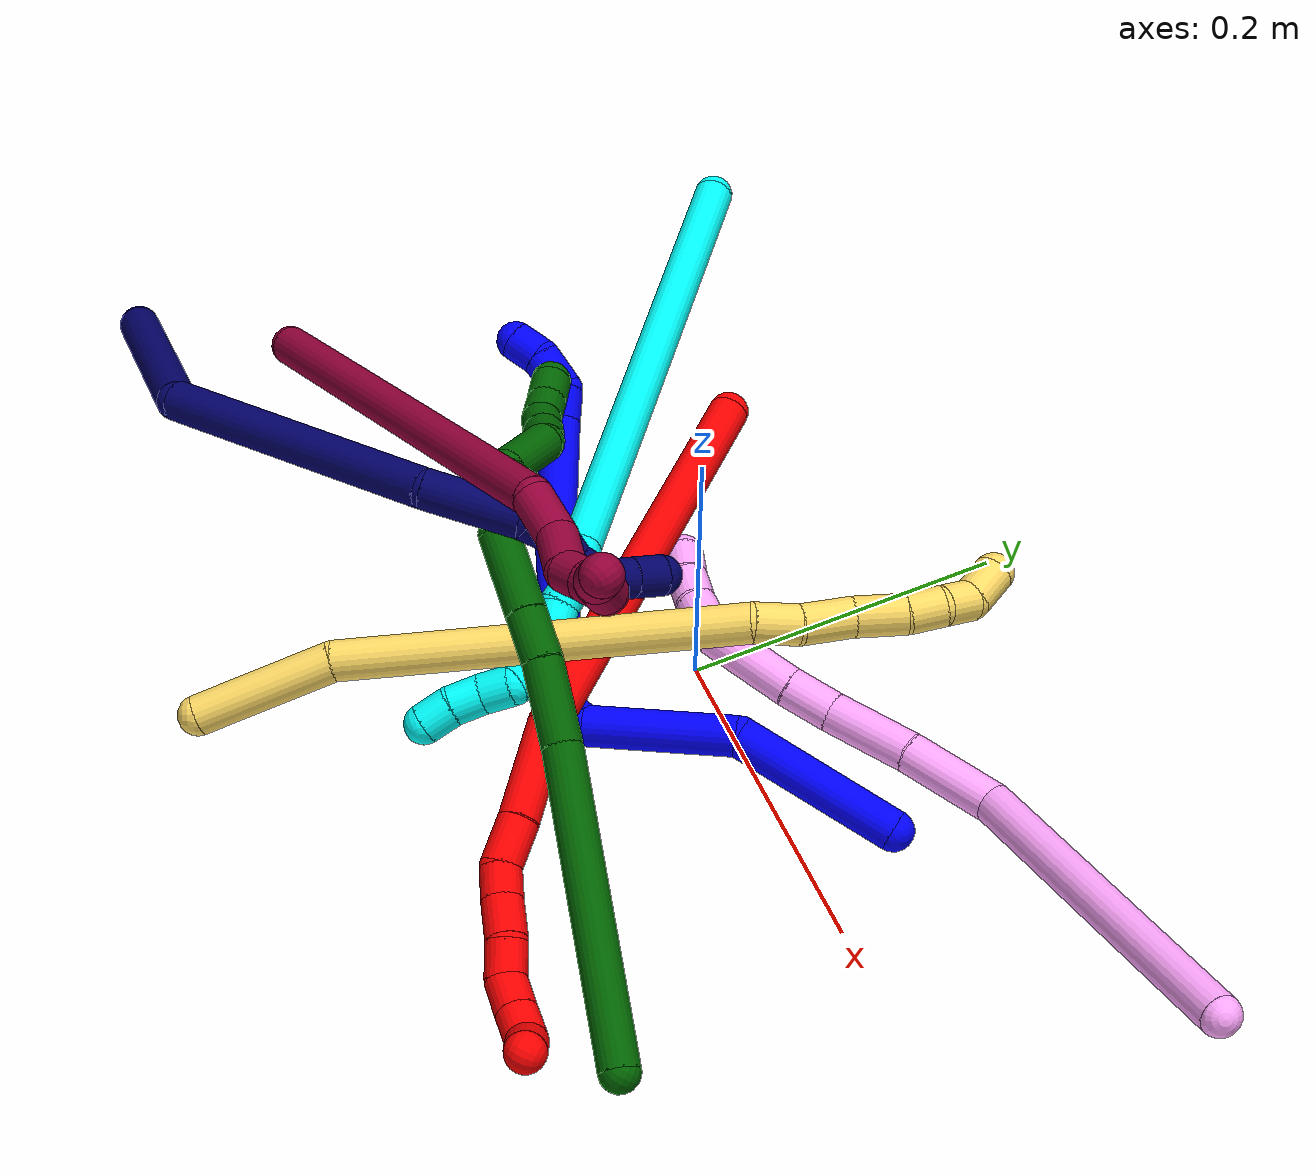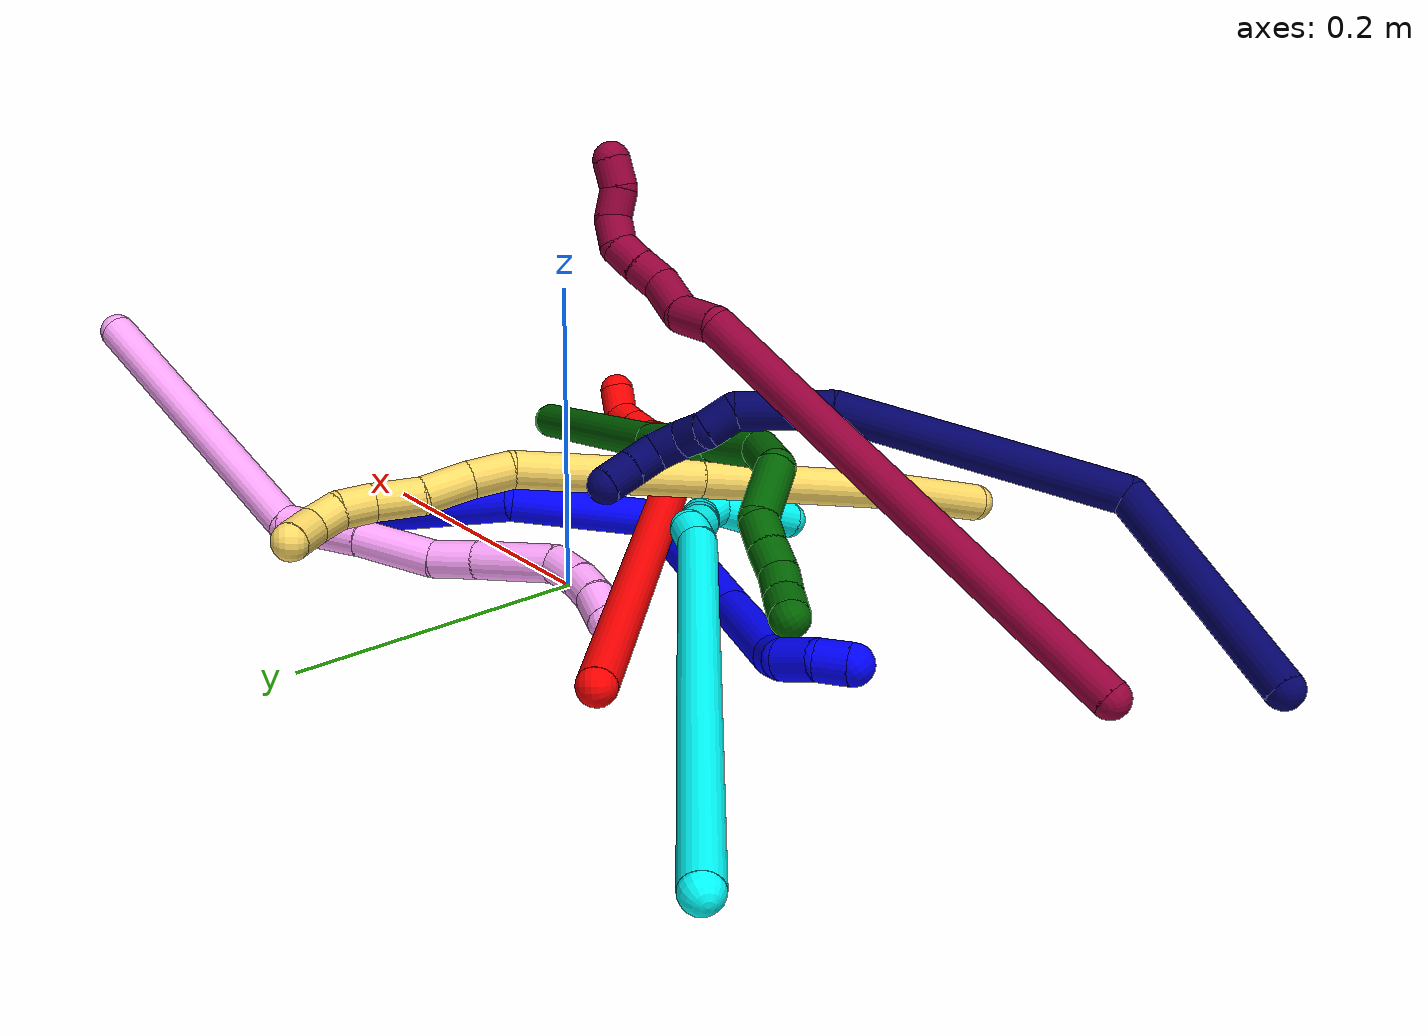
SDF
<sdf version="1.7">
 <world name="default">
  <plugin name="TubeGeneratorPlugin" filename="libtube_generator_plugin.so"/>
  <model name="photoneo_s_sensor">
   <static>1</static>
   <pose>0 0 2 1.57079 1.57079 3.14159</pose>
   <link name="link">
    <inertial><mass>0.1</mass></inertial>
    <sensor name="sensor" type="depth">
     <update_rate>30</update_rate>
     <camera>
      <horizontal_fov>1.22</horizontal_fov>
      <image><width>1920</width><height>1200</height><format>B8G8R8</format></image>
      <clip><near>0.1</near><far>4</far></clip>
      <depth_camera><output>points</output></depth_camera>
     </camera>
     <plugin name="camera_plugin" filename="libgazebo_ros_depth_camera.so">
      <baseline>0.2</baseline>
      <alwaysOn>1</alwaysOn>
      <updateRate>0.0</updateRate>
      <cameraName>camera_ir</cameraName>
      <imageTopicName>/camera/color/image_raw</imageTopicName>
      <cameraInfoTopicName>/camera/color/camera_info</cameraInfoTopicName>
      <depthImageTopicName>/camera/depth/image_raw</depthImageTopicName>
      <depthImageCameraInfoTopicName>/camera/depth/camera_info</depthImageCameraInfoTopicName>
      <pointCloudTopicName>/camera/depth/points</pointCloudTopicName>
      <frameName>fr_optical</frameName>
      <pointCloudCutoff>0.1</pointCloudCutoff>
      <pointCloudCutoffMax>2.0</pointCloudCutoffMax>
      <distortionK1>0</distortionK1>
      <distortionK2>0</distortionK2>
      <distortionK3>0</distortionK3>
      <distortionT1>0</distortionT1>
      <distortionT2>0</distortionT2>
      <CxPrime>0</CxPrime>
      <Cx>0</Cx>
      <Cy>0</Cy>
      <focalLength>0</focalLength>
      <hackBaseline>0</hackBaseline>
     </plugin>
    </sensor>
   </link>
  </model>
  <gravity>0 0 -9.8</gravity>
  <magnetic_field>6e-06 2.3e-05 -4.2e-05</magnetic_field>
  <atmosphere type="adiabatic"/>
  <physics name="default_physics" default="0" type="ode">
   <max_step_size>0.003</max_step_size>
   <real_time_factor>1</real_time_factor>
   <real_time_update_rate>1000</real_time_update_rate>
   <max_contacts>10000</max_contacts>
   <ode>
    <solver>
     <type>quick</type>
     <iters>100</iters>
     <sor>1.3</sor>
     <use_dynamic_moi_rescaling>0</use_dynamic_moi_rescaling>
    </solver>
    <constraints>
     <contact_max_correcting_vel>0</contact_max_correcting_vel>
     <contact_surface_layer>0.001</contact_surface_layer>
     <cfm>0</cfm>
     <erp>0.2</erp>
    </constraints>
   </ode>
  </physics>
  <scene><ambient>0.4 0.4 0.4 1</ambient><background>0.7 0.7 0.7 1</background><shadows>0</shadows></scene>
  <audio><device>default</device></audio>
  <spherical_coordinates>
   <surface_model>EARTH_WGS84</surface_model>
   <latitude_deg>0</latitude_deg>
   <longitude_deg>0</longitude_deg>
   <elevation>0</elevation>
   <heading_deg>0</heading_deg>
  </spherical_coordinates>
  <model name="bin">
   <static>1</static>
   <link name="bottom">
    <collision name="collision-bottom">
     <pose>0 0 -0.01 0 -0 0</pose>
     <geometry><box><size>0.8 0.6 0.02</size></box></geometry>
     <surface>
      <friction><ode><mu>100</mu><mu2>100</mu2></ode></friction>
      <contact><collide_bitmask>65535</collide_bitmask></contact>
     </surface>
    </collision>
   </link>
   <link name="west_wall">
    <collision name="collision-west_wall">
     <pose>-0.41 0 0.1 0 -0 0</pose>
     <geometry><box><size>0.02 0.6 0.2</size></box></geometry>
     <surface>
      <friction><ode><mu>100</mu><mu2>100</mu2></ode></friction>
      <contact><collide_bitmask>65535</collide_bitmask></contact>
     </surface>
    </collision>
   </link>
   <link name="east_wall">
    <collision name="collision-east_wall">
     <pose>0.41 0 0.1 0 -0 0</pose>
     <geometry><box><size>0.02 0.6 0.2</size></box></geometry>
     <surface>
      <friction><ode><mu>100</mu><mu2>100</mu2></ode></friction>
      <contact><collide_bitmask>65535</collide_bitmask></contact>
     </surface>
    </collision>
   </link>
   <link name="south_wall">
    <collision name="collision-south_wall">
     <pose>0 -0.31 0.1 0 -0 0</pose>
     <geometry><box><size>0.8 0.02 0.2</size></box></geometry>
     <surface>
      <friction><ode><mu>100</mu><mu2>100</mu2></ode></friction>
      <contact><collide_bitmask>65535</collide_bitmask></contact>
     </surface>
    </collision>
   </link>
   <link name="north_wall">
    <collision name="collision-north_wall">
     <pose>0 0.31 0.1 0 -0 0</pose>
     <geometry><box><size>0.8 0.02 0.2</size></box></geometry>
     <surface>
      <friction><ode><mu>100</mu><mu2>100</mu2></ode></friction>
      <contact><collide_bitmask>65535</collide_bitmask></contact>
     </surface>
    </collision>
   </link>
  </model>
  <model name="1">
   <static>0</static>
   <link name="1">
    <collision name="collision-cylinder-e_1_1_4">
     <pose>-0.032006 -0.033837 -0.02488 2.2048 -0.651176 -1.17684</pose>
     <geometry><cylinder><radius>0.0125</radius><length>0.10561</length></cylinder></geometry>
     <surface>
      <friction><ode><mu>1.16</mu><mu2>1.16</mu2><slip1>0</slip1><slip2>0</slip2></ode></friction>
      <contact><ode><kp>1e+06</kp><kd>1</kd><max_vel>0</max_vel><min_depth>0.001</min_depth></ode></contact>
     </surface>
    </collision>
    <visual name="visual-cylinder-e_1_1_4">
     <pose>-0.032006 -0.033837 -0.02488 2.2048 -0.651176 -1.17684</pose>
     <geometry><cylinder><radius>0.0125</radius><length>0.10561</length></cylinder></geometry>
     <material><ambient>0 0 1 1</ambient></material>
    </visual>
    <collision name="collision-cylinder-e_2_4_5">
     <pose>-0.072055 -0.10131 -0.080643 2.31358 -0.174344 -0.39266</pose>
     <geometry><cylinder><radius>0.0125</radius><length>0.092733</length></cylinder></geometry>
     <surface>
      <friction><ode><mu>1.16</mu><mu2>1.16</mu2><slip1>0</slip1><slip2>0</slip2></ode></friction>
      <contact><ode><kp>1e+06</kp><kd>1</kd><max_vel>0</max_vel><min_depth>0.001</min_depth></ode></contact>
     </surface>
    </collision>
    <visual name="visual-cylinder-e_2_4_5">
     <pose>-0.072055 -0.10131 -0.080643 2.31358 -0.174344 -0.39266</pose>
     <geometry><cylinder><radius>0.0125</radius><length>0.092733</length></cylinder></geometry>
     <material><ambient>0 0 1 1</ambient></material>
    </visual>
    <collision name="collision-cylinder-e_3_5_6">
     <pose>-0.085355 -0.135998 -0.120915 3.02995 -0.507812 -2.71743</pose>
     <geometry><cylinder><radius>0.0125</radius><length>0.021622</length></cylinder></geometry>
     <surface>
      <friction><ode><mu>1.16</mu><mu2>1.16</mu2><slip1>0</slip1><slip2>0</slip2></ode></friction>
      <contact><ode><kp>1e+06</kp><kd>1</kd><max_vel>0</max_vel><min_depth>0.001</min_depth></ode></contact>
     </surface>
    </collision>
    <visual name="visual-cylinder-e_3_5_6">
     <pose>-0.085355 -0.135998 -0.120915 3.02995 -0.507812 -2.71743</pose>
     <geometry><cylinder><radius>0.0125</radius><length>0.021622</length></cylinder></geometry>
     <material><ambient>0 0 1 1</ambient></material>
    </visual>
    <collision name="collision-cylinder-e_4_6_7">
     <pose>-0.142732 -0.12016 -0.156476 -2.56852 -1.03212 2.18358</pose>
     <geometry><cylinder><radius>0.0125</radius><length>0.121438</length></cylinder></geometry>
     <surface>
      <friction><ode><mu>1.16</mu><mu2>1.16</mu2><slip1>0</slip1><slip2>0</slip2></ode></friction>
      <contact><ode><kp>1e+06</kp><kd>1</kd><max_vel>0</max_vel><min_depth>0.001</min_depth></ode></contact>
     </surface>
    </collision>
    <visual name="visual-cylinder-e_4_6_7">
     <pose>-0.142732 -0.12016 -0.156476 -2.56852 -1.03212 2.18358</pose>
     <geometry><cylinder><radius>0.0125</radius><length>0.121438</length></cylinder></geometry>
     <material><ambient>0 0 1 1</ambient></material>
    </visual>
    <collision name="collision-cylinder-e_5_7_8">
     <pose>-0.23585 -0.089684 -0.195618 -2.33296 -1.14118 1.96554</pose>
     <geometry><cylinder><radius>0.0125</radius><length>0.090192</length></cylinder></geometry>
     <surface>
      <friction><ode><mu>1.16</mu><mu2>1.16</mu2><slip1>0</slip1><slip2>0</slip2></ode></friction>
      <contact><ode><kp>1e+06</kp><kd>1</kd><max_vel>0</max_vel><min_depth>0.001</min_depth></ode></contact>
     </surface>
    </collision>
    <visual name="visual-cylinder-e_5_7_8">
     <pose>-0.23585 -0.089684 -0.195618 -2.33296 -1.14118 1.96554</pose>
     <geometry><cylinder><radius>0.0125</radius><length>0.090192</length></cylinder></geometry>
     <material><ambient>0 0 1 1</ambient></material>
    </visual>
    <collision name="collision-cylinder-e_6_8_9">
     <pose>-0.287565 -0.073432 -0.209363 -1.85385 -1.31738 1.60153</pose>
     <geometry><cylinder><radius>0.0125</radius><length>0.022141</length></cylinder></geometry>
     <surface>
      <friction><ode><mu>1.16</mu><mu2>1.16</mu2><slip1>0</slip1><slip2>0</slip2></ode></friction>
      <contact><ode><kp>1e+06</kp><kd>1</kd><max_vel>0</max_vel><min_depth>0.001</min_depth></ode></contact>
     </surface>
    </collision>
    <visual name="visual-cylinder-e_6_8_9">
     <pose>-0.287565 -0.073432 -0.209363 -1.85385 -1.31738 1.60153</pose>
     <geometry><cylinder><radius>0.0125</radius><length>0.022141</length></cylinder></geometry>
     <material><ambient>0 0 1 1</ambient></material>
    </visual>
    <collision name="collision-cylinder-e_7_9_10">
     <pose>-0.309508 -0.075106 -0.214825 2.39478 -1.05354 -1.95594</pose>
     <geometry><cylinder><radius>0.0125</radius><length>0.025832</length></cylinder></geometry>
     <surface>
      <friction><ode><mu>1.16</mu><mu2>1.16</mu2><slip1>0</slip1><slip2>0</slip2></ode></friction>
      <contact><ode><kp>1e+06</kp><kd>1</kd><max_vel>0</max_vel><min_depth>0.001</min_depth></ode></contact>
     </surface>
    </collision>
    <visual name="visual-cylinder-e_7_9_10">
     <pose>-0.309508 -0.075106 -0.214825 2.39478 -1.05354 -1.95594</pose>
     <geometry><cylinder><radius>0.0125</radius><length>0.025832</length></cylinder></geometry>
     <material><ambient>0 0 1 1</ambient></material>
    </visual>
    <collision name="collision-cylinder-e_8_10_2">
     <pose>-0.327318 -0.084466 -0.225497 2.44352 -0.700195 -1.5741</pose>
     <geometry><cylinder><radius>0.0125</radius><length>0.020433</length></cylinder></geometry>
     <surface>
      <friction><ode><mu>1.16</mu><mu2>1.16</mu2><slip1>0</slip1><slip2>0</slip2></ode></friction>
      <contact><ode><kp>1e+06</kp><kd>1</kd><max_vel>0</max_vel><min_depth>0.001</min_depth></ode></contact>
     </surface>
    </collision>
    <visual name="visual-cylinder-e_8_10_2">
     <pose>-0.327318 -0.084466 -0.225497 2.44352 -0.700195 -1.5741</pose>
     <geometry><cylinder><radius>0.0125</radius><length>0.020433</length></cylinder></geometry>
     <material><ambient>0 0 1 1</ambient></material>
    </visual>
    <collision name="collision-sphere-2">
     <pose>-0.333901 -0.089488 -0.231482 0 -0 0</pose>
     <geometry><sphere><radius>0.0125</radius></sphere></geometry>
     <surface>
      <friction><ode><mu>1.16</mu><mu2>1.16</mu2><slip1>0</slip1><slip2>0</slip2></ode></friction>
      <contact><ode><kp>1e+06</kp><kd>1</kd><max_vel>0</max_vel><min_depth>0.001</min_depth></ode></contact>
     </surface>
    </collision>
    <visual name="visual-sphere-2">
     <pose>-0.333901 -0.089488 -0.231482 0 -0 0</pose>
     <geometry><sphere><radius>0.0125</radius></sphere></geometry>
     <material><ambient>0 0 1 1</ambient></material>
    </visual>
    <collision name="collision-sphere-10">
     <pose>-0.320735 -0.079444 -0.219512 0 -0 0</pose>
     <geometry><sphere><radius>0.0125</radius></sphere></geometry>
     <surface>
      <friction><ode><mu>1.16</mu><mu2>1.16</mu2><slip1>0</slip1><slip2>0</slip2></ode></friction>
      <contact><ode><kp>1e+06</kp><kd>1</kd><max_vel>0</max_vel><min_depth>0.001</min_depth></ode></contact>
     </surface>
    </collision>
    <visual name="visual-sphere-10">
     <pose>-0.320735 -0.079444 -0.219512 0 -0 0</pose>
     <geometry><sphere><radius>0.0125</radius></sphere></geometry>
     <material><ambient>0 0 1 1</ambient></material>
    </visual>
    <collision name="collision-sphere-9">
     <pose>-0.298282 -0.070767 -0.210138 0 -0 0</pose>
     <geometry><sphere><radius>0.0125</radius></sphere></geometry>
     <surface>
      <friction><ode><mu>1.16</mu><mu2>1.16</mu2><slip1>0</slip1><slip2>0</slip2></ode></friction>
      <contact><ode><kp>1e+06</kp><kd>1</kd><max_vel>0</max_vel><min_depth>0.001</min_depth></ode></contact>
     </surface>
    </collision>
    <visual name="visual-sphere-9">
     <pose>-0.298282 -0.070767 -0.210138 0 -0 0</pose>
     <geometry><sphere><radius>0.0125</radius></sphere></geometry>
     <material><ambient>0 0 1 1</ambient></material>
    </visual>
    <collision name="collision-sphere-4">
     <pose>-0.064012 -0.067675 -0.049759 0 -0 0</pose>
     <geometry><sphere><radius>0.0125</radius></sphere></geometry>
     <surface>
      <friction><ode><mu>1.16</mu><mu2>1.16</mu2><slip1>0</slip1><slip2>0</slip2></ode></friction>
      <contact><ode><kp>1e+06</kp><kd>1</kd><max_vel>0</max_vel><min_depth>0.001</min_depth></ode></contact>
     </surface>
    </collision>
    <visual name="visual-sphere-4">
     <pose>-0.064012 -0.067675 -0.049759 0 -0 0</pose>
     <geometry><sphere><radius>0.0125</radius></sphere></geometry>
     <material><ambient>0 0 1 1</ambient></material>
    </visual>
    <collision name="collision-sphere-1">
     <geometry><sphere><radius>0.0125</radius></sphere></geometry>
     <surface>
      <friction><ode><mu>1.16</mu><mu2>1.16</mu2><slip1>0</slip1><slip2>0</slip2></ode></friction>
      <contact><ode><kp>1e+06</kp><kd>1</kd><max_vel>0</max_vel><min_depth>0.001</min_depth></ode></contact>
     </surface>
    </collision>
    <visual name="visual-sphere-1">
     <geometry><sphere><radius>0.0125</radius></sphere></geometry>
     <material><ambient>0 0 1 1</ambient></material>
    </visual>
    <collision name="collision-sphere-8">
     <pose>-0.276848 -0.076097 -0.208587 0 -0 0</pose>
     <geometry><sphere><radius>0.0125</radius></sphere></geometry>
     <surface>
      <friction><ode><mu>1.16</mu><mu2>1.16</mu2><slip1>0</slip1><slip2>0</slip2></ode></friction>
      <contact><ode><kp>1e+06</kp><kd>1</kd><max_vel>0</max_vel><min_depth>0.001</min_depth></ode></contact>
     </surface>
    </collision>
    <visual name="visual-sphere-8">
     <pose>-0.276848 -0.076097 -0.208587 0 -0 0</pose>
     <geometry><sphere><radius>0.0125</radius></sphere></geometry>
     <material><ambient>0 0 1 1</ambient></material>
    </visual>
    <collision name="collision-sphere-5">
     <pose>-0.080098 -0.134945 -0.111527 0 -0 0</pose>
     <geometry><sphere><radius>0.0125</radius></sphere></geometry>
     <surface>
      <friction><ode><mu>1.16</mu><mu2>1.16</mu2><slip1>0</slip1><slip2>0</slip2></ode></friction>
      <contact><ode><kp>1e+06</kp><kd>1</kd><max_vel>0</max_vel><min_depth>0.001</min_depth></ode></contact>
     </surface>
    </collision>
    <visual name="visual-sphere-5">
     <pose>-0.080098 -0.134945 -0.111527 0 -0 0</pose>
     <geometry><sphere><radius>0.0125</radius></sphere></geometry>
     <material><ambient>0 0 1 1</ambient></material>
    </visual>
    <collision name="collision-sphere-6">
     <pose>-0.090612 -0.13705 -0.130303 0 -0 0</pose>
     <geometry><sphere><radius>0.0125</radius></sphere></geometry>
     <surface>
      <friction><ode><mu>1.16</mu><mu2>1.16</mu2><slip1>0</slip1><slip2>0</slip2></ode></friction>
      <contact><ode><kp>1e+06</kp><kd>1</kd><max_vel>0</max_vel><min_depth>0.001</min_depth></ode></contact>
     </surface>
    </collision>
    <visual name="visual-sphere-6">
     <pose>-0.090612 -0.13705 -0.130303 0 -0 0</pose>
     <geometry><sphere><radius>0.0125</radius></sphere></geometry>
     <material><ambient>0 0 1 1</ambient></material>
    </visual>
    <collision name="collision-sphere-7">
     <pose>-0.194852 -0.103271 -0.182648 0 -0 0</pose>
     <geometry><sphere><radius>0.0125</radius></sphere></geometry>
     <surface>
      <friction><ode><mu>1.16</mu><mu2>1.16</mu2><slip1>0</slip1><slip2>0</slip2></ode></friction>
      <contact><ode><kp>1e+06</kp><kd>1</kd><max_vel>0</max_vel><min_depth>0.001</min_depth></ode></contact>
     </surface>
    </collision>
    <visual name="visual-sphere-7">
     <pose>-0.194852 -0.103271 -0.182648 0 -0 0</pose>
     <geometry><sphere><radius>0.0125</radius></sphere></geometry>
     <material><ambient>0 0 1 1</ambient></material>
    </visual>
    <inertial>
     <pose>-0.143126 -0.087763 -0.128316 0 -0 0</pose>
     <mass>0.5</mass>
     <inertia><ixx>-3e-06</ixx><ixy>0</ixy><ixz>0</ixz><iyy>0.000156</iyy><iyz>0</iyz><izz>0.000308</izz></inertia>
    </inertial>
   </link>
   <pose>0.157265 0.054039 0.012408 -0.461743 0.542385 -0.302729</pose>
  </model>
  <model name="2">
   <static>0</static>
   <link name="2">
    <collision name="collision-cylinder-e_1_1_4">
     <pose>0.135381 0.020114 -0.002061 -1.6729 1.42254 -1.5243</pose>
     <geometry><cylinder><radius>0.0125</radius><length>0.273765</length></cylinder></geometry>
     <surface>
      <friction><ode><mu>1.16</mu><mu2>1.16</mu2><slip1>0</slip1><slip2>0</slip2></ode></friction>
      <contact><ode><kp>1e+06</kp><kd>1</kd><max_vel>0</max_vel><min_depth>0.001</min_depth></ode></contact>
     </surface>
    </collision>
    <visual name="visual-cylinder-e_1_1_4">
     <pose>0.135381 0.020114 -0.002061 -1.6729 1.42254 -1.5243</pose>
     <geometry><cylinder><radius>0.0125</radius><length>0.273765</length></cylinder></geometry>
     <material><ambient>1 0 0 1</ambient></material>
    </visual>
    <collision name="collision-cylinder-e_2_4_5">
     <pose>0.301775 0.038496 -0.0102 2.86397 1.36976 2.80277</pose>
     <geometry><cylinder><radius>0.0125</radius><length>0.063301</length></cylinder></geometry>
     <surface>
      <friction><ode><mu>1.16</mu><mu2>1.16</mu2><slip1>0</slip1><slip2>0</slip2></ode></friction>
      <contact><ode><kp>1e+06</kp><kd>1</kd><max_vel>0</max_vel><min_depth>0.001</min_depth></ode></contact>
     </surface>
    </collision>
    <visual name="visual-cylinder-e_2_4_5">
     <pose>0.301775 0.038496 -0.0102 2.86397 1.36976 2.80277</pose>
     <geometry><cylinder><radius>0.0125</radius><length>0.063301</length></cylinder></geometry>
     <material><ambient>1 0 0 1</ambient></material>
    </visual>
    <collision name="collision-cylinder-e_3_5_6">
     <pose>0.347435 0.035097 -0.018086 2.39688 1.40445 2.27665</pose>
     <geometry><cylinder><radius>0.0125</radius><length>0.029703</length></cylinder></geometry>
     <surface>
      <friction><ode><mu>1.16</mu><mu2>1.16</mu2><slip1>0</slip1><slip2>0</slip2></ode></friction>
      <contact><ode><kp>1e+06</kp><kd>1</kd><max_vel>0</max_vel><min_depth>0.001</min_depth></ode></contact>
     </surface>
    </collision>
    <visual name="visual-cylinder-e_3_5_6">
     <pose>0.347435 0.035097 -0.018086 2.39688 1.40445 2.27665</pose>
     <geometry><cylinder><radius>0.0125</radius><length>0.029703</length></cylinder></geometry>
     <material><ambient>1 0 0 1</ambient></material>
    </visual>
    <collision name="collision-cylinder-e_4_6_7">
     <pose>0.370806 0.032756 -0.024939 3.00873 1.04277 2.91096</pose>
     <geometry><cylinder><radius>0.0125</radius><length>0.020203</length></cylinder></geometry>
     <surface>
      <friction><ode><mu>1.16</mu><mu2>1.16</mu2><slip1>0</slip1><slip2>0</slip2></ode></friction>
      <contact><ode><kp>1e+06</kp><kd>1</kd><max_vel>0</max_vel><min_depth>0.001</min_depth></ode></contact>
     </surface>
    </collision>
    <visual name="visual-cylinder-e_4_6_7">
     <pose>0.370806 0.032756 -0.024939 3.00873 1.04277 2.91096</pose>
     <geometry><cylinder><radius>0.0125</radius><length>0.020203</length></cylinder></geometry>
     <material><ambient>1 0 0 1</ambient></material>
    </visual>
    <collision name="collision-cylinder-e_5_7_8">
     <pose>0.390534 0.0335 -0.036885 -2.93889 1.0012 -2.774</pose>
     <geometry><cylinder><radius>0.0125</radius><length>0.026129</length></cylinder></geometry>
     <surface>
      <friction><ode><mu>1.16</mu><mu2>1.16</mu2><slip1>0</slip1><slip2>0</slip2></ode></friction>
      <contact><ode><kp>1e+06</kp><kd>1</kd><max_vel>0</max_vel><min_depth>0.001</min_depth></ode></contact>
     </surface>
    </collision>
    <visual name="visual-cylinder-e_5_7_8">
     <pose>0.390534 0.0335 -0.036885 -2.93889 1.0012 -2.774</pose>
     <geometry><cylinder><radius>0.0125</radius><length>0.026129</length></cylinder></geometry>
     <material><ambient>1 0 0 1</ambient></material>
    </visual>
    <collision name="collision-cylinder-e_6_8_9">
     <pose>0.411528 0.032927 -0.048697 2.75643 1.08318 2.51469</pose>
     <geometry><cylinder><radius>0.0125</radius><length>0.022621</length></cylinder></geometry>
     <surface>
      <friction><ode><mu>1.16</mu><mu2>1.16</mu2><slip1>0</slip1><slip2>0</slip2></ode></friction>
      <contact><ode><kp>1e+06</kp><kd>1</kd><max_vel>0</max_vel><min_depth>0.001</min_depth></ode></contact>
     </surface>
    </collision>
    <visual name="visual-cylinder-e_6_8_9">
     <pose>0.411528 0.032927 -0.048697 2.75643 1.08318 2.51469</pose>
     <geometry><cylinder><radius>0.0125</radius><length>0.022621</length></cylinder></geometry>
     <material><ambient>1 0 0 1</ambient></material>
    </visual>
    <collision name="collision-cylinder-e_7_9_10">
     <pose>0.429665 0.033542 -0.060996 -2.80245 0.804805 -2.37668</pose>
     <geometry><cylinder><radius>0.0125</radius><length>0.022599</length></cylinder></geometry>
     <surface>
      <friction><ode><mu>1.16</mu><mu2>1.16</mu2><slip1>0</slip1><slip2>0</slip2></ode></friction>
      <contact><ode><kp>1e+06</kp><kd>1</kd><max_vel>0</max_vel><min_depth>0.001</min_depth></ode></contact>
     </surface>
    </collision>
    <visual name="visual-cylinder-e_7_9_10">
     <pose>0.429665 0.033542 -0.060996 -2.80245 0.804805 -2.37668</pose>
     <geometry><cylinder><radius>0.0125</radius><length>0.022599</length></cylinder></geometry>
     <material><ambient>1 0 0 1</ambient></material>
    </visual>
    <collision name="collision-cylinder-e_8_10_11">
     <pose>0.445019 0.038748 -0.075113 -2.77301 0.785146 -2.29557</pose>
     <geometry><cylinder><radius>0.0125</radius><length>0.0204</length></cylinder></geometry>
     <surface>
      <friction><ode><mu>1.16</mu><mu2>1.16</mu2><slip1>0</slip1><slip2>0</slip2></ode></friction>
      <contact><ode><kp>1e+06</kp><kd>1</kd><max_vel>0</max_vel><min_depth>0.001</min_depth></ode></contact>
     </surface>
    </collision>
    <visual name="visual-cylinder-e_8_10_11">
     <pose>0.445019 0.038748 -0.075113 -2.77301 0.785146 -2.29557</pose>
     <geometry><cylinder><radius>0.0125</radius><length>0.0204</length></cylinder></geometry>
     <material><ambient>1 0 0 1</ambient></material>
    </visual>
    <collision name="collision-cylinder-e_9_11_2">
     <pose>0.45826 0.049895 -0.083783 -1.79396 0.602578 -0.742277</pose>
     <geometry><cylinder><radius>0.0125</radius><length>0.021278</length></cylinder></geometry>
     <surface>
      <friction><ode><mu>1.16</mu><mu2>1.16</mu2><slip1>0</slip1><slip2>0</slip2></ode></friction>
      <contact><ode><kp>1e+06</kp><kd>1</kd><max_vel>0</max_vel><min_depth>0.001</min_depth></ode></contact>
     </surface>
    </collision>
    <visual name="visual-cylinder-e_9_11_2">
     <pose>0.45826 0.049895 -0.083783 -1.79396 0.602578 -0.742277</pose>
     <geometry><cylinder><radius>0.0125</radius><length>0.021278</length></cylinder></geometry>
     <material><ambient>1 0 0 1</ambient></material>
    </visual>
    <collision name="collision-sphere-2">
     <pose>0.464289 0.058443 -0.085723 0 -0 0</pose>
     <geometry><sphere><radius>0.0125</radius></sphere></geometry>
     <surface>
      <friction><ode><mu>1.16</mu><mu2>1.16</mu2><slip1>0</slip1><slip2>0</slip2></ode></friction>
      <contact><ode><kp>1e+06</kp><kd>1</kd><max_vel>0</max_vel><min_depth>0.001</min_depth></ode></contact>
     </surface>
    </collision>
    <visual name="visual-sphere-2">
     <pose>0.464289 0.058443 -0.085723 0 -0 0</pose>
     <geometry><sphere><radius>0.0125</radius></sphere></geometry>
     <material><ambient>1 0 0 1</ambient></material>
    </visual>
    <collision name="collision-sphere-11">
     <pose>0.45223 0.041347 -0.081843 0 -0 0</pose>
     <geometry><sphere><radius>0.0125</radius></sphere></geometry>
     <surface>
      <friction><ode><mu>1.16</mu><mu2>1.16</mu2><slip1>0</slip1><slip2>0</slip2></ode></friction>
      <contact><ode><kp>1e+06</kp><kd>1</kd><max_vel>0</max_vel><min_depth>0.001</min_depth></ode></contact>
     </surface>
    </collision>
    <visual name="visual-sphere-11">
     <pose>0.45223 0.041347 -0.081843 0 -0 0</pose>
     <geometry><sphere><radius>0.0125</radius></sphere></geometry>
     <material><ambient>1 0 0 1</ambient></material>
    </visual>
    <collision name="collision-sphere-10">
     <pose>0.437808 0.036149 -0.068383 0 -0 0</pose>
     <geometry><sphere><radius>0.0125</radius></sphere></geometry>
     <surface>
      <friction><ode><mu>1.16</mu><mu2>1.16</mu2><slip1>0</slip1><slip2>0</slip2></ode></friction>
      <contact><ode><kp>1e+06</kp><kd>1</kd><max_vel>0</max_vel><min_depth>0.001</min_depth></ode></contact>
     </surface>
    </collision>
    <visual name="visual-sphere-10">
     <pose>0.437808 0.036149 -0.068383 0 -0 0</pose>
     <geometry><sphere><radius>0.0125</radius></sphere></geometry>
     <material><ambient>1 0 0 1</ambient></material>
    </visual>
    <collision name="collision-sphere-9">
     <pose>0.421521 0.030936 -0.053608 0 -0 0</pose>
     <geometry><sphere><radius>0.0125</radius></sphere></geometry>
     <surface>
      <friction><ode><mu>1.16</mu><mu2>1.16</mu2><slip1>0</slip1><slip2>0</slip2></ode></friction>
      <contact><ode><kp>1e+06</kp><kd>1</kd><max_vel>0</max_vel><min_depth>0.001</min_depth></ode></contact>
     </surface>
    </collision>
    <visual name="visual-sphere-9">
     <pose>0.421521 0.030936 -0.053608 0 -0 0</pose>
     <geometry><sphere><radius>0.0125</radius></sphere></geometry>
     <material><ambient>1 0 0 1</ambient></material>
    </visual>
    <collision name="collision-sphere-4">
     <pose>0.270762 0.040228 -0.004122 0 -0 0</pose>
     <geometry><sphere><radius>0.0125</radius></sphere></geometry>
     <surface>
      <friction><ode><mu>1.16</mu><mu2>1.16</mu2><slip1>0</slip1><slip2>0</slip2></ode></friction>
      <contact><ode><kp>1e+06</kp><kd>1</kd><max_vel>0</max_vel><min_depth>0.001</min_depth></ode></contact>
     </surface>
    </collision>
    <visual name="visual-sphere-4">
     <pose>0.270762 0.040228 -0.004122 0 -0 0</pose>
     <geometry><sphere><radius>0.0125</radius></sphere></geometry>
     <material><ambient>1 0 0 1</ambient></material>
    </visual>
    <collision name="collision-sphere-1">
     <geometry><sphere><radius>0.0125</radius></sphere></geometry>
     <surface>
      <friction><ode><mu>1.16</mu><mu2>1.16</mu2><slip1>0</slip1><slip2>0</slip2></ode></friction>
      <contact><ode><kp>1e+06</kp><kd>1</kd><max_vel>0</max_vel><min_depth>0.001</min_depth></ode></contact>
     </surface>
    </collision>
    <visual name="visual-sphere-1">
     <geometry><sphere><radius>0.0125</radius></sphere></geometry>
     <material><ambient>1 0 0 1</ambient></material>
    </visual>
    <collision name="collision-sphere-8">
     <pose>0.401536 0.034918 -0.043786 0 -0 0</pose>
     <geometry><sphere><radius>0.0125</radius></sphere></geometry>
     <surface>
      <friction><ode><mu>1.16</mu><mu2>1.16</mu2><slip1>0</slip1><slip2>0</slip2></ode></friction>
      <contact><ode><kp>1e+06</kp><kd>1</kd><max_vel>0</max_vel><min_depth>0.001</min_depth></ode></contact>
     </surface>
    </collision>
    <visual name="visual-sphere-8">
     <pose>0.401536 0.034918 -0.043786 0 -0 0</pose>
     <geometry><sphere><radius>0.0125</radius></sphere></geometry>
     <material><ambient>1 0 0 1</ambient></material>
    </visual>
    <collision name="collision-sphere-5">
     <pose>0.332788 0.036763 -0.016278 0 -0 0</pose>
     <geometry><sphere><radius>0.0125</radius></sphere></geometry>
     <surface>
      <friction><ode><mu>1.16</mu><mu2>1.16</mu2><slip1>0</slip1><slip2>0</slip2></ode></friction>
      <contact><ode><kp>1e+06</kp><kd>1</kd><max_vel>0</max_vel><min_depth>0.001</min_depth></ode></contact>
     </surface>
    </collision>
    <visual name="visual-sphere-5">
     <pose>0.332788 0.036763 -0.016278 0 -0 0</pose>
     <geometry><sphere><radius>0.0125</radius></sphere></geometry>
     <material><ambient>1 0 0 1</ambient></material>
    </visual>
    <collision name="collision-sphere-6">
     <pose>0.362081 0.03343 -0.019894 0 -0 0</pose>
     <geometry><sphere><radius>0.0125</radius></sphere></geometry>
     <surface>
      <friction><ode><mu>1.16</mu><mu2>1.16</mu2><slip1>0</slip1><slip2>0</slip2></ode></friction>
      <contact><ode><kp>1e+06</kp><kd>1</kd><max_vel>0</max_vel><min_depth>0.001</min_depth></ode></contact>
     </surface>
    </collision>
    <visual name="visual-sphere-6">
     <pose>0.362081 0.03343 -0.019894 0 -0 0</pose>
     <geometry><sphere><radius>0.0125</radius></sphere></geometry>
     <material><ambient>1 0 0 1</ambient></material>
    </visual>
    <collision name="collision-sphere-7">
     <pose>0.379532 0.032082 -0.029983 0 -0 0</pose>
     <geometry><sphere><radius>0.0125</radius></sphere></geometry>
     <surface>
      <friction><ode><mu>1.16</mu><mu2>1.16</mu2><slip1>0</slip1><slip2>0</slip2></ode></friction>
      <contact><ode><kp>1e+06</kp><kd>1</kd><max_vel>0</max_vel><min_depth>0.001</min_depth></ode></contact>
     </surface>
    </collision>
    <visual name="visual-sphere-7">
     <pose>0.379532 0.032082 -0.029983 0 -0 0</pose>
     <geometry><sphere><radius>0.0125</radius></sphere></geometry>
     <material><ambient>1 0 0 1</ambient></material>
    </visual>
    <inertial>
     <pose>0.244059 0.027756 -0.01802 0 -0 0</pose>
     <mass>0.5</mass>
     <inertia>
      <ixx>-0.000214</ixx>
      <ixy>0</ixy>
      <ixz>0</ixz>
      <iyy>0.001469</iyy>
      <iyz>0</iyz>
      <izz>-0.001996</izz>
     </inertia>
    </inertial>
   </link>
   <pose>-0.15797 0.095948 0.023295 1.43203 0.079623 -0.874722</pose>
  </model>
  <model name="3">
   <static>0</static>
   <link name="3">
    <collision name="collision-cylinder-e_1_1_4">
     <pose>0.004202 -0.043896 0.161614 0.265214 0.025087 0.003346</pose>
     <geometry><cylinder><radius>0.0125</radius><length>0.335045</length></cylinder></geometry>
     <surface>
      <friction><ode><mu>1.16</mu><mu2>1.16</mu2><slip1>0</slip1><slip2>0</slip2></ode></friction>
      <contact><ode><kp>1e+06</kp><kd>1</kd><max_vel>0</max_vel><min_depth>0.001</min_depth></ode></contact>
     </surface>
    </collision>
    <visual name="visual-cylinder-e_1_1_4">
     <pose>0.004202 -0.043896 0.161614 0.265214 0.025087 0.003346</pose>
     <geometry><cylinder><radius>0.0125</radius><length>0.335045</length></cylinder></geometry>
     <material><ambient>0.003922 1 0.996078 1</ambient></material>
    </visual>
    <collision name="collision-cylinder-e_2_4_5">
     <pose>0.009357 -0.088173 0.33351 0.036997 0.092378 0.00171</pose>
     <geometry><cylinder><radius>0.0125</radius><length>0.020666</length></cylinder></geometry>
     <surface>
      <friction><ode><mu>1.16</mu><mu2>1.16</mu2><slip1>0</slip1><slip2>0</slip2></ode></friction>
      <contact><ode><kp>1e+06</kp><kd>1</kd><max_vel>0</max_vel><min_depth>0.001</min_depth></ode></contact>
     </surface>
    </collision>
    <visual name="visual-cylinder-e_2_4_5">
     <pose>0.009357 -0.088173 0.33351 0.036997 0.092378 0.00171</pose>
     <geometry><cylinder><radius>0.0125</radius><length>0.020666</length></cylinder></geometry>
     <material><ambient>0.003922 1 0.996078 1</ambient></material>
    </visual>
    <collision name="collision-cylinder-e_3_5_6">
     <pose>0.013859 -0.095132 0.353095 0.615528 0.301919 0.09663</pose>
     <geometry><cylinder><radius>0.0125</radius><length>0.023866</length></cylinder></geometry>
     <surface>
      <friction><ode><mu>1.16</mu><mu2>1.16</mu2><slip1>0</slip1><slip2>0</slip2></ode></friction>
      <contact><ode><kp>1e+06</kp><kd>1</kd><max_vel>0</max_vel><min_depth>0.001</min_depth></ode></contact>
     </surface>
    </collision>
    <visual name="visual-cylinder-e_3_5_6">
     <pose>0.013859 -0.095132 0.353095 0.615528 0.301919 0.09663</pose>
     <geometry><cylinder><radius>0.0125</radius><length>0.023866</length></cylinder></geometry>
     <material><ambient>0.003922 1 0.996078 1</ambient></material>
    </visual>
    <collision name="collision-cylinder-e_4_6_7">
     <pose>0.02161 -0.104902 0.371054 0.353176 0.427443 0.07742</pose>
     <geometry><cylinder><radius>0.0125</radius><length>0.020277</length></cylinder></geometry>
     <surface>
      <friction><ode><mu>1.16</mu><mu2>1.16</mu2><slip1>0</slip1><slip2>0</slip2></ode></friction>
      <contact><ode><kp>1e+06</kp><kd>1</kd><max_vel>0</max_vel><min_depth>0.001</min_depth></ode></contact>
     </surface>
    </collision>
    <visual name="visual-cylinder-e_4_6_7">
     <pose>0.02161 -0.104902 0.371054 0.353176 0.427443 0.07742</pose>
     <geometry><cylinder><radius>0.0125</radius><length>0.020277</length></cylinder></geometry>
     <material><ambient>0.003922 1 0.996078 1</ambient></material>
    </visual>
    <collision name="collision-cylinder-e_5_7_8">
     <pose>0.029818 -0.111386 0.388313 0.365614 0.410133 0.076865</pose>
     <geometry><cylinder><radius>0.0125</radius><length>0.020087</length></cylinder></geometry>
     <surface>
      <friction><ode><mu>1.16</mu><mu2>1.16</mu2><slip1>0</slip1><slip2>0</slip2></ode></friction>
      <contact><ode><kp>1e+06</kp><kd>1</kd><max_vel>0</max_vel><min_depth>0.001</min_depth></ode></contact>
     </surface>
    </collision>
    <visual name="visual-cylinder-e_5_7_8">
     <pose>0.029818 -0.111386 0.388313 0.365614 0.410133 0.076865</pose>
     <geometry><cylinder><radius>0.0125</radius><length>0.020087</length></cylinder></geometry>
     <material><ambient>0.003922 1 0.996078 1</ambient></material>
    </visual>
    <collision name="collision-cylinder-e_6_8_9">
     <pose>0.033579 -0.122455 0.403207 0.89043 -0.024336 -0.011613</pose>
     <geometry><cylinder><radius>0.0125</radius><length>0.020013</length></cylinder></geometry>
     <surface>
      <friction><ode><mu>1.16</mu><mu2>1.16</mu2><slip1>0</slip1><slip2>0</slip2></ode></friction>
      <contact><ode><kp>1e+06</kp><kd>1</kd><max_vel>0</max_vel><min_depth>0.001</min_depth></ode></contact>
     </surface>
    </collision>
    <visual name="visual-cylinder-e_6_8_9">
     <pose>0.033579 -0.122455 0.403207 0.89043 -0.024336 -0.011613</pose>
     <geometry><cylinder><radius>0.0125</radius><length>0.020013</length></cylinder></geometry>
     <material><ambient>0.003922 1 0.996078 1</ambient></material>
    </visual>
    <collision name="collision-cylinder-e_7_9_10">
     <pose>0.035977 -0.139899 0.409479 1.57296 0.266765 0.267335</pose>
     <geometry><cylinder><radius>0.0125</radius><length>0.020044</length></cylinder></geometry>
     <surface>
      <friction><ode><mu>1.16</mu><mu2>1.16</mu2><slip1>0</slip1><slip2>0</slip2></ode></friction>
      <contact><ode><kp>1e+06</kp><kd>1</kd><max_vel>0</max_vel><min_depth>0.001</min_depth></ode></contact>
     </surface>
    </collision>
    <visual name="visual-cylinder-e_7_9_10">
     <pose>0.035977 -0.139899 0.409479 1.57296 0.266765 0.267335</pose>
     <geometry><cylinder><radius>0.0125</radius><length>0.020044</length></cylinder></geometry>
     <material><ambient>0.003922 1 0.996078 1</ambient></material>
    </visual>
    <collision name="collision-cylinder-e_8_10_11">
     <pose>0.040339 -0.159169 0.411658 1.34562 0.172809 0.137826</pose>
     <geometry><cylinder><radius>0.0125</radius><length>0.02</length></cylinder></geometry>
     <surface>
      <friction><ode><mu>1.16</mu><mu2>1.16</mu2><slip1>0</slip1><slip2>0</slip2></ode></friction>
      <contact><ode><kp>1e+06</kp><kd>1</kd><max_vel>0</max_vel><min_depth>0.001</min_depth></ode></contact>
     </surface>
    </collision>
    <visual name="visual-cylinder-e_8_10_11">
     <pose>0.040339 -0.159169 0.411658 1.34562 0.172809 0.137826</pose>
     <geometry><cylinder><radius>0.0125</radius><length>0.02</length></cylinder></geometry>
     <material><ambient>0.003922 1 0.996078 1</ambient></material>
    </visual>
    <collision name="collision-cylinder-e_9_11_2">
     <pose>0.045454 -0.177603 0.417097 1.2192 0.346381 0.243128</pose>
     <geometry><cylinder><radius>0.0125</radius><length>0.020001</length></cylinder></geometry>
     <surface>
      <friction><ode><mu>1.16</mu><mu2>1.16</mu2><slip1>0</slip1><slip2>0</slip2></ode></friction>
      <contact><ode><kp>1e+06</kp><kd>1</kd><max_vel>0</max_vel><min_depth>0.001</min_depth></ode></contact>
     </surface>
    </collision>
    <visual name="visual-cylinder-e_9_11_2">
     <pose>0.045454 -0.177603 0.417097 1.2192 0.346381 0.243128</pose>
     <geometry><cylinder><radius>0.0125</radius><length>0.020001</length></cylinder></geometry>
     <material><ambient>0.003922 1 0.996078 1</ambient></material>
    </visual>
    <collision name="collision-sphere-2">
     <pose>0.048849 -0.186434 0.420337 0 -0 0</pose>
     <geometry><sphere><radius>0.0125</radius></sphere></geometry>
     <surface>
      <friction><ode><mu>1.16</mu><mu2>1.16</mu2><slip1>0</slip1><slip2>0</slip2></ode></friction>
      <contact><ode><kp>1e+06</kp><kd>1</kd><max_vel>0</max_vel><min_depth>0.001</min_depth></ode></contact>
     </surface>
    </collision>
    <visual name="visual-sphere-2">
     <pose>0.048849 -0.186434 0.420337 0 -0 0</pose>
     <geometry><sphere><radius>0.0125</radius></sphere></geometry>
     <material><ambient>0.003922 1 0.996078 1</ambient></material>
    </visual>
    <collision name="collision-sphere-11">
     <pose>0.042058 -0.168772 0.413858 0 -0 0</pose>
     <geometry><sphere><radius>0.0125</radius></sphere></geometry>
     <surface>
      <friction><ode><mu>1.16</mu><mu2>1.16</mu2><slip1>0</slip1><slip2>0</slip2></ode></friction>
      <contact><ode><kp>1e+06</kp><kd>1</kd><max_vel>0</max_vel><min_depth>0.001</min_depth></ode></contact>
     </surface>
    </collision>
    <visual name="visual-sphere-11">
     <pose>0.042058 -0.168772 0.413858 0 -0 0</pose>
     <geometry><sphere><radius>0.0125</radius></sphere></geometry>
     <material><ambient>0.003922 1 0.996078 1</ambient></material>
    </visual>
    <collision name="collision-sphere-10">
     <pose>0.038619 -0.149567 0.409459 0 -0 0</pose>
     <geometry><sphere><radius>0.0125</radius></sphere></geometry>
     <surface>
      <friction><ode><mu>1.16</mu><mu2>1.16</mu2><slip1>0</slip1><slip2>0</slip2></ode></friction>
      <contact><ode><kp>1e+06</kp><kd>1</kd><max_vel>0</max_vel><min_depth>0.001</min_depth></ode></contact>
     </surface>
    </collision>
    <visual name="visual-sphere-10">
     <pose>0.038619 -0.149567 0.409459 0 -0 0</pose>
     <geometry><sphere><radius>0.0125</radius></sphere></geometry>
     <material><ambient>0.003922 1 0.996078 1</ambient></material>
    </visual>
    <collision name="collision-sphere-9">
     <pose>0.033335 -0.130232 0.4095 0 -0 0</pose>
     <geometry><sphere><radius>0.0125</radius></sphere></geometry>
     <surface>
      <friction><ode><mu>1.16</mu><mu2>1.16</mu2><slip1>0</slip1><slip2>0</slip2></ode></friction>
      <contact><ode><kp>1e+06</kp><kd>1</kd><max_vel>0</max_vel><min_depth>0.001</min_depth></ode></contact>
     </surface>
    </collision>
    <visual name="visual-sphere-9">
     <pose>0.033335 -0.130232 0.4095 0 -0 0</pose>
     <geometry><sphere><radius>0.0125</radius></sphere></geometry>
     <material><ambient>0.003922 1 0.996078 1</ambient></material>
    </visual>
    <collision name="collision-sphere-4">
     <pose>0.008404 -0.087793 0.323229 0 -0 0</pose>
     <geometry><sphere><radius>0.0125</radius></sphere></geometry>
     <surface>
      <friction><ode><mu>1.16</mu><mu2>1.16</mu2><slip1>0</slip1><slip2>0</slip2></ode></friction>
      <contact><ode><kp>1e+06</kp><kd>1</kd><max_vel>0</max_vel><min_depth>0.001</min_depth></ode></contact>
     </surface>
    </collision>
    <visual name="visual-sphere-4">
     <pose>0.008404 -0.087793 0.323229 0 -0 0</pose>
     <geometry><sphere><radius>0.0125</radius></sphere></geometry>
     <material><ambient>0.003922 1 0.996078 1</ambient></material>
    </visual>
    <collision name="collision-sphere-1">
     <geometry><sphere><radius>0.0125</radius></sphere></geometry>
     <surface>
      <friction><ode><mu>1.16</mu><mu2>1.16</mu2><slip1>0</slip1><slip2>0</slip2></ode></friction>
      <contact><ode><kp>1e+06</kp><kd>1</kd><max_vel>0</max_vel><min_depth>0.001</min_depth></ode></contact>
     </surface>
    </collision>
    <visual name="visual-sphere-1">
     <geometry><sphere><radius>0.0125</radius></sphere></geometry>
     <material><ambient>0.003922 1 0.996078 1</ambient></material>
    </visual>
    <collision name="collision-sphere-8">
     <pose>0.033822 -0.114679 0.396914 0 -0 0</pose>
     <geometry><sphere><radius>0.0125</radius></sphere></geometry>
     <surface>
      <friction><ode><mu>1.16</mu><mu2>1.16</mu2><slip1>0</slip1><slip2>0</slip2></ode></friction>
      <contact><ode><kp>1e+06</kp><kd>1</kd><max_vel>0</max_vel><min_depth>0.001</min_depth></ode></contact>
     </surface>
    </collision>
    <visual name="visual-sphere-8">
     <pose>0.033822 -0.114679 0.396914 0 -0 0</pose>
     <geometry><sphere><radius>0.0125</radius></sphere></geometry>
     <material><ambient>0.003922 1 0.996078 1</ambient></material>
    </visual>
    <collision name="collision-sphere-5">
     <pose>0.010311 -0.088554 0.343792 0 -0 0</pose>
     <geometry><sphere><radius>0.0125</radius></sphere></geometry>
     <surface>
      <friction><ode><mu>1.16</mu><mu2>1.16</mu2><slip1>0</slip1><slip2>0</slip2></ode></friction>
      <contact><ode><kp>1e+06</kp><kd>1</kd><max_vel>0</max_vel><min_depth>0.001</min_depth></ode></contact>
     </surface>
    </collision>
    <visual name="visual-sphere-5">
     <pose>0.010311 -0.088554 0.343792 0 -0 0</pose>
     <geometry><sphere><radius>0.0125</radius></sphere></geometry>
     <material><ambient>0.003922 1 0.996078 1</ambient></material>
    </visual>
    <collision name="collision-sphere-6">
     <pose>0.017407 -0.101711 0.362397 0 -0 0</pose>
     <geometry><sphere><radius>0.0125</radius></sphere></geometry>
     <surface>
      <friction><ode><mu>1.16</mu><mu2>1.16</mu2><slip1>0</slip1><slip2>0</slip2></ode></friction>
      <contact><ode><kp>1e+06</kp><kd>1</kd><max_vel>0</max_vel><min_depth>0.001</min_depth></ode></contact>
     </surface>
    </collision>
    <visual name="visual-sphere-6">
     <pose>0.017407 -0.101711 0.362397 0 -0 0</pose>
     <geometry><sphere><radius>0.0125</radius></sphere></geometry>
     <material><ambient>0.003922 1 0.996078 1</ambient></material>
    </visual>
    <collision name="collision-sphere-7">
     <pose>0.025813 -0.108093 0.379711 0 -0 0</pose>
     <geometry><sphere><radius>0.0125</radius></sphere></geometry>
     <surface>
      <friction><ode><mu>1.16</mu><mu2>1.16</mu2><slip1>0</slip1><slip2>0</slip2></ode></friction>
      <contact><ode><kp>1e+06</kp><kd>1</kd><max_vel>0</max_vel><min_depth>0.001</min_depth></ode></contact>
     </surface>
    </collision>
    <visual name="visual-sphere-7">
     <pose>0.025813 -0.108093 0.379711 0 -0 0</pose>
     <geometry><sphere><radius>0.0125</radius></sphere></geometry>
     <material><ambient>0.003922 1 0.996078 1</ambient></material>
    </visual>
    <inertial>
     <pose>0.012157 -0.07031 0.235288 0 -0 0</pose>
     <mass>0.5</mass>
     <inertia>
      <ixx>0.003174</ixx>
      <ixy>0</ixy>
      <ixz>0</ixz>
      <iyy>0.003043</iyy>
      <iyz>0</iyz>
      <izz>0.000783</izz>
     </inertia>
    </inertial>
   </link>
   <pose>-0.339614 0.170526 0.012433 0.645011 1.35998 0.232861</pose>
  </model>
  <model name="4">
   <static>0</static>
   <link name="4">
    <collision name="collision-cylinder-e_1_1_4">
     <pose>-0.053953 0.01799 -0.098352 -2.96068 -0.49484 2.45209</pose>
     <geometry><cylinder><radius>0.0125</radius><length>0.227225</length></cylinder></geometry>
     <surface>
      <friction><ode><mu>1.16</mu><mu2>1.16</mu2><slip1>0</slip1><slip2>0</slip2></ode></friction>
      <contact><ode><kp>1e+06</kp><kd>1</kd><max_vel>0</max_vel><min_depth>0.001</min_depth></ode></contact>
     </surface>
    </collision>
    <visual name="visual-cylinder-e_1_1_4">
     <pose>-0.053953 0.01799 -0.098352 -2.96068 -0.49484 2.45209</pose>
     <geometry><cylinder><radius>0.0125</radius><length>0.227225</length></cylinder></geometry>
     <material><ambient>1 0.65098 0.996078 1</ambient></material>
    </visual>
    <collision name="collision-cylinder-e_2_4_5">
     <pose>-0.133263 0.037095 -0.211459 -3.06617 -1.04256 3.01038</pose>
     <geometry><cylinder><radius>0.0125</radius><length>0.058716</length></cylinder></geometry>
     <surface>
      <friction><ode><mu>1.16</mu><mu2>1.16</mu2><slip1>0</slip1><slip2>0</slip2></ode></friction>
      <contact><ode><kp>1e+06</kp><kd>1</kd><max_vel>0</max_vel><min_depth>0.001</min_depth></ode></contact>
     </surface>
    </collision>
    <visual name="visual-cylinder-e_2_4_5">
     <pose>-0.133263 0.037095 -0.211459 -3.06617 -1.04256 3.01038</pose>
     <geometry><cylinder><radius>0.0125</radius><length>0.058716</length></cylinder></geometry>
     <material><ambient>1 0.65098 0.996078 1</ambient></material>
    </visual>
    <collision name="collision-cylinder-e_3_5_6">
     <pose>-0.181345 0.037523 -0.241586 3.0969 -0.975585 -3.05739</pose>
     <geometry><cylinder><radius>0.0125</radius><length>0.05489</length></cylinder></geometry>
     <surface>
      <friction><ode><mu>1.16</mu><mu2>1.16</mu2><slip1>0</slip1><slip2>0</slip2></ode></friction>
      <contact><ode><kp>1e+06</kp><kd>1</kd><max_vel>0</max_vel><min_depth>0.001</min_depth></ode></contact>
     </surface>
    </collision>
    <visual name="visual-cylinder-e_3_5_6">
     <pose>-0.181345 0.037523 -0.241586 3.0969 -0.975585 -3.05739</pose>
     <geometry><cylinder><radius>0.0125</radius><length>0.05489</length></cylinder></geometry>
     <material><ambient>1 0.65098 0.996078 1</ambient></material>
    </visual>
    <collision name="collision-cylinder-e_4_6_7">
     <pose>-0.21853 0.037222 -0.262476 -3.0715 -1.20548 3.03978</pose>
     <geometry><cylinder><radius>0.0125</radius><length>0.030964</length></cylinder></geometry>
     <surface>
      <friction><ode><mu>1.16</mu><mu2>1.16</mu2><slip1>0</slip1><slip2>0</slip2></ode></friction>
      <contact><ode><kp>1e+06</kp><kd>1</kd><max_vel>0</max_vel><min_depth>0.001</min_depth></ode></contact>
     </surface>
    </collision>
    <visual name="visual-cylinder-e_4_6_7">
     <pose>-0.21853 0.037222 -0.262476 -3.0715 -1.20548 3.03978</pose>
     <geometry><cylinder><radius>0.0125</radius><length>0.030964</length></cylinder></geometry>
     <material><ambient>1 0.65098 0.996078 1</ambient></material>
    </visual>
    <collision name="collision-cylinder-e_5_7_8">
     <pose>-0.258693 0.040225 -0.278794 -2.904 -1.1627 2.78222</pose>
     <geometry><cylinder><radius>0.0125</radius><length>0.056003</length></cylinder></geometry>
     <surface>
      <friction><ode><mu>1.16</mu><mu2>1.16</mu2><slip1>0</slip1><slip2>0</slip2></ode></friction>
      <contact><ode><kp>1e+06</kp><kd>1</kd><max_vel>0</max_vel><min_depth>0.001</min_depth></ode></contact>
     </surface>
    </collision>
    <visual name="visual-cylinder-e_5_7_8">
     <pose>-0.258693 0.040225 -0.278794 -2.904 -1.1627 2.78222</pose>
     <geometry><cylinder><radius>0.0125</radius><length>0.056003</length></cylinder></geometry>
     <material><ambient>1 0.65098 0.996078 1</ambient></material>
    </visual>
    <collision name="collision-cylinder-e_6_8_9">
     <pose>-0.292488 0.048873 -0.299263 -2.58383 -0.617541 1.6785</pose>
     <geometry><cylinder><radius>0.0125</radius><length>0.027955</length></cylinder></geometry>
     <surface>
      <friction><ode><mu>1.16</mu><mu2>1.16</mu2><slip1>0</slip1><slip2>0</slip2></ode></friction>
      <contact><ode><kp>1e+06</kp><kd>1</kd><max_vel>0</max_vel><min_depth>0.001</min_depth></ode></contact>
     </surface>
    </collision>
    <visual name="visual-cylinder-e_6_8_9">
     <pose>-0.292488 0.048873 -0.299263 -2.58383 -0.617541 1.6785</pose>
     <geometry><cylinder><radius>0.0125</radius><length>0.027955</length></cylinder></geometry>
     <material><ambient>1 0.65098 0.996078 1</ambient></material>
    </visual>
    <collision name="collision-cylinder-e_7_9_10">
     <pose>-0.305027 0.060132 -0.316897 -2.56082 -0.436582 1.27712</pose>
     <geometry><cylinder><radius>0.0125</radius><length>0.021026</length></cylinder></geometry>
     <surface>
      <friction><ode><mu>1.16</mu><mu2>1.16</mu2><slip1>0</slip1><slip2>0</slip2></ode></friction>
      <contact><ode><kp>1e+06</kp><kd>1</kd><max_vel>0</max_vel><min_depth>0.001</min_depth></ode></contact>
     </surface>
    </collision>
    <visual name="visual-cylinder-e_7_9_10">
     <pose>-0.305027 0.060132 -0.316897 -2.56082 -0.436582 1.27712</pose>
     <geometry><cylinder><radius>0.0125</radius><length>0.021026</length></cylinder></geometry>
     <material><ambient>1 0.65098 0.996078 1</ambient></material>
    </visual>
    <collision name="collision-cylinder-e_8_10_2">
     <pose>-0.312492 0.070988 -0.334558 -2.61558 -0.263064 0.91342</pose>
     <geometry><cylinder><radius>0.0125</radius><length>0.023221</length></cylinder></geometry>
     <surface>
      <friction><ode><mu>1.16</mu><mu2>1.16</mu2><slip1>0</slip1><slip2>0</slip2></ode></friction>
      <contact><ode><kp>1e+06</kp><kd>1</kd><max_vel>0</max_vel><min_depth>0.001</min_depth></ode></contact>
     </surface>
    </collision>
    <visual name="visual-cylinder-e_8_10_2">
     <pose>-0.312492 0.070988 -0.334558 -2.61558 -0.263064 0.91342</pose>
     <geometry><cylinder><radius>0.0125</radius><length>0.023221</length></cylinder></geometry>
     <material><ambient>1 0.65098 0.996078 1</ambient></material>
    </visual>
    <collision name="collision-sphere-2">
     <pose>-0.315511 0.076617 -0.344253 0 -0 0</pose>
     <geometry><sphere><radius>0.0125</radius></sphere></geometry>
     <surface>
      <friction><ode><mu>1.16</mu><mu2>1.16</mu2><slip1>0</slip1><slip2>0</slip2></ode></friction>
      <contact><ode><kp>1e+06</kp><kd>1</kd><max_vel>0</max_vel><min_depth>0.001</min_depth></ode></contact>
     </surface>
    </collision>
    <visual name="visual-sphere-2">
     <pose>-0.315511 0.076617 -0.344253 0 -0 0</pose>
     <geometry><sphere><radius>0.0125</radius></sphere></geometry>
     <material><ambient>1 0.65098 0.996078 1</ambient></material>
    </visual>
    <collision name="collision-sphere-10">
     <pose>-0.309473 0.065359 -0.324862 0 -0 0</pose>
     <geometry><sphere><radius>0.0125</radius></sphere></geometry>
     <surface>
      <friction><ode><mu>1.16</mu><mu2>1.16</mu2><slip1>0</slip1><slip2>0</slip2></ode></friction>
      <contact><ode><kp>1e+06</kp><kd>1</kd><max_vel>0</max_vel><min_depth>0.001</min_depth></ode></contact>
     </surface>
    </collision>
    <visual name="visual-sphere-10">
     <pose>-0.309473 0.065359 -0.324862 0 -0 0</pose>
     <geometry><sphere><radius>0.0125</radius></sphere></geometry>
     <material><ambient>1 0.65098 0.996078 1</ambient></material>
    </visual>
    <collision name="collision-sphere-9">
     <pose>-0.300582 0.054904 -0.308932 0 -0 0</pose>
     <geometry><sphere><radius>0.0125</radius></sphere></geometry>
     <surface>
      <friction><ode><mu>1.16</mu><mu2>1.16</mu2><slip1>0</slip1><slip2>0</slip2></ode></friction>
      <contact><ode><kp>1e+06</kp><kd>1</kd><max_vel>0</max_vel><min_depth>0.001</min_depth></ode></contact>
     </surface>
    </collision>
    <visual name="visual-sphere-9">
     <pose>-0.300582 0.054904 -0.308932 0 -0 0</pose>
     <geometry><sphere><radius>0.0125</radius></sphere></geometry>
     <material><ambient>1 0.65098 0.996078 1</ambient></material>
    </visual>
    <collision name="collision-sphere-4">
     <pose>-0.107907 0.03598 -0.196704 0 -0 0</pose>
     <geometry><sphere><radius>0.0125</radius></sphere></geometry>
     <surface>
      <friction><ode><mu>1.16</mu><mu2>1.16</mu2><slip1>0</slip1><slip2>0</slip2></ode></friction>
      <contact><ode><kp>1e+06</kp><kd>1</kd><max_vel>0</max_vel><min_depth>0.001</min_depth></ode></contact>
     </surface>
    </collision>
    <visual name="visual-sphere-4">
     <pose>-0.107907 0.03598 -0.196704 0 -0 0</pose>
     <geometry><sphere><radius>0.0125</radius></sphere></geometry>
     <material><ambient>1 0.65098 0.996078 1</ambient></material>
    </visual>
    <collision name="collision-sphere-1">
     <geometry><sphere><radius>0.0125</radius></sphere></geometry>
     <surface>
      <friction><ode><mu>1.16</mu><mu2>1.16</mu2><slip1>0</slip1><slip2>0</slip2></ode></friction>
      <contact><ode><kp>1e+06</kp><kd>1</kd><max_vel>0</max_vel><min_depth>0.001</min_depth></ode></contact>
     </surface>
    </collision>
    <visual name="visual-sphere-1">
     <geometry><sphere><radius>0.0125</radius></sphere></geometry>
     <material><ambient>1 0.65098 0.996078 1</ambient></material>
    </visual>
    <collision name="collision-sphere-8">
     <pose>-0.284395 0.042841 -0.289594 0 -0 0</pose>
     <geometry><sphere><radius>0.0125</radius></sphere></geometry>
     <surface>
      <friction><ode><mu>1.16</mu><mu2>1.16</mu2><slip1>0</slip1><slip2>0</slip2></ode></friction>
      <contact><ode><kp>1e+06</kp><kd>1</kd><max_vel>0</max_vel><min_depth>0.001</min_depth></ode></contact>
     </surface>
    </collision>
    <visual name="visual-sphere-8">
     <pose>-0.284395 0.042841 -0.289594 0 -0 0</pose>
     <geometry><sphere><radius>0.0125</radius></sphere></geometry>
     <material><ambient>1 0.65098 0.996078 1</ambient></material>
    </visual>
    <collision name="collision-sphere-5">
     <pose>-0.15862 0.03821 -0.226214 0 -0 0</pose>
     <geometry><sphere><radius>0.0125</radius></sphere></geometry>
     <surface>
      <friction><ode><mu>1.16</mu><mu2>1.16</mu2><slip1>0</slip1><slip2>0</slip2></ode></friction>
      <contact><ode><kp>1e+06</kp><kd>1</kd><max_vel>0</max_vel><min_depth>0.001</min_depth></ode></contact>
     </surface>
    </collision>
    <visual name="visual-sphere-5">
     <pose>-0.15862 0.03821 -0.226214 0 -0 0</pose>
     <geometry><sphere><radius>0.0125</radius></sphere></geometry>
     <material><ambient>1 0.65098 0.996078 1</ambient></material>
    </visual>
    <collision name="collision-sphere-6">
     <pose>-0.20407 0.036835 -0.256959 0 -0 0</pose>
     <geometry><sphere><radius>0.0125</radius></sphere></geometry>
     <surface>
      <friction><ode><mu>1.16</mu><mu2>1.16</mu2><slip1>0</slip1><slip2>0</slip2></ode></friction>
      <contact><ode><kp>1e+06</kp><kd>1</kd><max_vel>0</max_vel><min_depth>0.001</min_depth></ode></contact>
     </surface>
    </collision>
    <visual name="visual-sphere-6">
     <pose>-0.20407 0.036835 -0.256959 0 -0 0</pose>
     <geometry><sphere><radius>0.0125</radius></sphere></geometry>
     <material><ambient>1 0.65098 0.996078 1</ambient></material>
    </visual>
    <collision name="collision-sphere-7">
     <pose>-0.232991 0.03761 -0.267993 0 -0 0</pose>
     <geometry><sphere><radius>0.0125</radius></sphere></geometry>
     <surface>
      <friction><ode><mu>1.16</mu><mu2>1.16</mu2><slip1>0</slip1><slip2>0</slip2></ode></friction>
      <contact><ode><kp>1e+06</kp><kd>1</kd><max_vel>0</max_vel><min_depth>0.001</min_depth></ode></contact>
     </surface>
    </collision>
    <visual name="visual-sphere-7">
     <pose>-0.232991 0.03761 -0.267993 0 -0 0</pose>
     <geometry><sphere><radius>0.0125</radius></sphere></geometry>
     <material><ambient>1 0.65098 0.996078 1</ambient></material>
    </visual>
    <inertial>
     <pose>-0.146278 0.032019 -0.189126 0 -0 0</pose>
     <mass>0.5</mass>
     <inertia>
      <ixx>-0.000159</ixx>
      <ixy>0</ixy>
      <ixz>0</ixz>
      <iyy>0.001424</iyy>
      <iyz>0</iyz>
      <izz>0.000332</izz>
     </inertia>
    </inertial>
   </link>
   <pose>0.377524 0.128912 0.103312 0.625055 0.403045 0.826723</pose>
  </model>
  <model name="5">
   <static>0</static>
   <link name="5">
    <collision name="collision-cylinder-e_1_1_4">
     <pose>0.01483 0.004798 -0.041065 -3.02529 0.344391 -2.49558</pose>
     <geometry><cylinder><radius>0.0125</radius><length>0.087847</length></cylinder></geometry>
     <surface>
      <friction><ode><mu>1.16</mu><mu2>1.16</mu2><slip1>0</slip1><slip2>0</slip2></ode></friction>
      <contact><ode><kp>1e+06</kp><kd>1</kd><max_vel>0</max_vel><min_depth>0.001</min_depth></ode></contact>
     </surface>
    </collision>
    <visual name="visual-cylinder-e_1_1_4">
     <pose>0.01483 0.004798 -0.041065 -3.02529 0.344391 -2.49558</pose>
     <geometry><cylinder><radius>0.0125</radius><length>0.087847</length></cylinder></geometry>
     <material><ambient>1 0.858824 0.4 1</ambient></material>
    </visual>
    <collision name="collision-cylinder-e_2_4_5">
     <pose>0.03426 0.01016 -0.144129 -3.13247 0.074075 -2.89675</pose>
     <geometry><cylinder><radius>0.0125</radius><length>0.124344</length></cylinder></geometry>
     <surface>
      <friction><ode><mu>1.16</mu><mu2>1.16</mu2><slip1>0</slip1><slip2>0</slip2></ode></friction>
      <contact><ode><kp>1e+06</kp><kd>1</kd><max_vel>0</max_vel><min_depth>0.001</min_depth></ode></contact>
     </surface>
    </collision>
    <visual name="visual-cylinder-e_2_4_5">
     <pose>0.03426 0.01016 -0.144129 -3.13247 0.074075 -2.89675</pose>
     <geometry><cylinder><radius>0.0125</radius><length>0.124344</length></cylinder></geometry>
     <material><ambient>1 0.858824 0.4 1</ambient></material>
    </visual>
    <collision name="collision-cylinder-e_3_5_6">
     <pose>0.043581 0.011722 -0.269293 -3.12582 0.074567 -2.72487</pose>
     <geometry><cylinder><radius>0.0125</radius><length>0.126699</length></cylinder></geometry>
     <surface>
      <friction><ode><mu>1.16</mu><mu2>1.16</mu2><slip1>0</slip1><slip2>0</slip2></ode></friction>
      <contact><ode><kp>1e+06</kp><kd>1</kd><max_vel>0</max_vel><min_depth>0.001</min_depth></ode></contact>
     </surface>
    </collision>
    <visual name="visual-cylinder-e_3_5_6">
     <pose>0.043581 0.011722 -0.269293 -3.12582 0.074567 -2.72487</pose>
     <geometry><cylinder><radius>0.0125</radius><length>0.126699</length></cylinder></geometry>
     <material><ambient>1 0.858824 0.4 1</ambient></material>
    </visual>
    <collision name="collision-cylinder-e_4_6_7">
     <pose>0.046481 0.015895 -0.346087 -2.91259 -0.129266 1.02521</pose>
     <geometry><cylinder><radius>0.0125</radius><length>0.028223</length></cylinder></geometry>
     <surface>
      <friction><ode><mu>1.16</mu><mu2>1.16</mu2><slip1>0</slip1><slip2>0</slip2></ode></friction>
      <contact><ode><kp>1e+06</kp><kd>1</kd><max_vel>0</max_vel><min_depth>0.001</min_depth></ode></contact>
     </surface>
    </collision>
    <visual name="visual-cylinder-e_4_6_7">
     <pose>0.046481 0.015895 -0.346087 -2.91259 -0.129266 1.02521</pose>
     <geometry><cylinder><radius>0.0125</radius><length>0.028223</length></cylinder></geometry>
     <material><ambient>1 0.858824 0.4 1</ambient></material>
    </visual>
    <collision name="collision-cylinder-e_5_7_8">
     <pose>0.044858 0.025574 -0.375043 -2.74038 0.011756 -0.0578</pose>
     <geometry><cylinder><radius>0.0125</radius><length>0.033301</length></cylinder></geometry>
     <surface>
      <friction><ode><mu>1.16</mu><mu2>1.16</mu2><slip1>0</slip1><slip2>0</slip2></ode></friction>
      <contact><ode><kp>1e+06</kp><kd>1</kd><max_vel>0</max_vel><min_depth>0.001</min_depth></ode></contact>
     </surface>
    </collision>
    <visual name="visual-cylinder-e_5_7_8">
     <pose>0.044858 0.025574 -0.375043 -2.74038 0.011756 -0.0578</pose>
     <geometry><cylinder><radius>0.0125</radius><length>0.033301</length></cylinder></geometry>
     <material><ambient>1 0.858824 0.4 1</ambient></material>
    </visual>
    <collision name="collision-cylinder-e_6_8_9">
     <pose>0.044881 0.034825 -0.406171 -2.96934 -0.01077 0.12458</pose>
     <geometry><cylinder><radius>0.0125</radius><length>0.032078</length></cylinder></geometry>
     <surface>
      <friction><ode><mu>1.16</mu><mu2>1.16</mu2><slip1>0</slip1><slip2>0</slip2></ode></friction>
      <contact><ode><kp>1e+06</kp><kd>1</kd><max_vel>0</max_vel><min_depth>0.001</min_depth></ode></contact>
     </surface>
    </collision>
    <visual name="visual-cylinder-e_6_8_9">
     <pose>0.044881 0.034825 -0.406171 -2.96934 -0.01077 0.12458</pose>
     <geometry><cylinder><radius>0.0125</radius><length>0.032078</length></cylinder></geometry>
     <material><ambient>1 0.858824 0.4 1</ambient></material>
    </visual>
    <collision name="collision-cylinder-e_7_9_10">
     <pose>0.045933 0.041206 -0.432597 -2.81224 0.10868 -0.63265</pose>
     <geometry><cylinder><radius>0.0125</radius><length>0.022591</length></cylinder></geometry>
     <surface>
      <friction><ode><mu>1.16</mu><mu2>1.16</mu2><slip1>0</slip1><slip2>0</slip2></ode></friction>
      <contact><ode><kp>1e+06</kp><kd>1</kd><max_vel>0</max_vel><min_depth>0.001</min_depth></ode></contact>
     </surface>
    </collision>
    <visual name="visual-cylinder-e_7_9_10">
     <pose>0.045933 0.041206 -0.432597 -2.81224 0.10868 -0.63265</pose>
     <geometry><cylinder><radius>0.0125</radius><length>0.022591</length></cylinder></geometry>
     <material><ambient>1 0.858824 0.4 1</ambient></material>
    </visual>
    <collision name="collision-cylinder-e_8_10_11">
     <pose>0.047091 0.050753 -0.451357 -2.51279 -0.006715 0.020648</pose>
     <geometry><cylinder><radius>0.0125</radius><length>0.020116</length></cylinder></geometry>
     <surface>
      <friction><ode><mu>1.16</mu><mu2>1.16</mu2><slip1>0</slip1><slip2>0</slip2></ode></friction>
      <contact><ode><kp>1e+06</kp><kd>1</kd><max_vel>0</max_vel><min_depth>0.001</min_depth></ode></contact>
     </surface>
    </collision>
    <visual name="visual-cylinder-e_8_10_11">
     <pose>0.047091 0.050753 -0.451357 -2.51279 -0.006715 0.020648</pose>
     <geometry><cylinder><radius>0.0125</radius><length>0.020116</length></cylinder></geometry>
     <material><ambient>1 0.858824 0.4 1</ambient></material>
    </visual>
    <collision name="collision-cylinder-e_9_11_2">
     <pose>0.052683 0.06535 -0.466302 -2.23606 0.473904 -0.92154</pose>
     <geometry><cylinder><radius>0.0125</radius><length>0.024801</length></cylinder></geometry>
     <surface>
      <friction><ode><mu>1.16</mu><mu2>1.16</mu2><slip1>0</slip1><slip2>0</slip2></ode></friction>
      <contact><ode><kp>1e+06</kp><kd>1</kd><max_vel>0</max_vel><min_depth>0.001</min_depth></ode></contact>
     </surface>
    </collision>
    <visual name="visual-cylinder-e_9_11_2">
     <pose>0.052683 0.06535 -0.466302 -2.23606 0.473904 -0.92154</pose>
     <geometry><cylinder><radius>0.0125</radius><length>0.024801</length></cylinder></geometry>
     <material><ambient>1 0.858824 0.4 1</ambient></material>
    </visual>
    <collision name="collision-sphere-2">
     <pose>0.058342 0.074031 -0.473112 0 -0 0</pose>
     <geometry><sphere><radius>0.0125</radius></sphere></geometry>
     <surface>
      <friction><ode><mu>1.16</mu><mu2>1.16</mu2><slip1>0</slip1><slip2>0</slip2></ode></friction>
      <contact><ode><kp>1e+06</kp><kd>1</kd><max_vel>0</max_vel><min_depth>0.001</min_depth></ode></contact>
     </surface>
    </collision>
    <visual name="visual-sphere-2">
     <pose>0.058342 0.074031 -0.473112 0 -0 0</pose>
     <geometry><sphere><radius>0.0125</radius></sphere></geometry>
     <material><ambient>1 0.858824 0.4 1</ambient></material>
    </visual>
    <collision name="collision-sphere-11">
     <pose>0.047023 0.056669 -0.459491 0 -0 0</pose>
     <geometry><sphere><radius>0.0125</radius></sphere></geometry>
     <surface>
      <friction><ode><mu>1.16</mu><mu2>1.16</mu2><slip1>0</slip1><slip2>0</slip2></ode></friction>
      <contact><ode><kp>1e+06</kp><kd>1</kd><max_vel>0</max_vel><min_depth>0.001</min_depth></ode></contact>
     </surface>
    </collision>
    <visual name="visual-sphere-11">
     <pose>0.047023 0.056669 -0.459491 0 -0 0</pose>
     <geometry><sphere><radius>0.0125</radius></sphere></geometry>
     <material><ambient>1 0.858824 0.4 1</ambient></material>
    </visual>
    <collision name="collision-sphere-10">
     <pose>0.047158 0.044837 -0.443223 0 -0 0</pose>
     <geometry><sphere><radius>0.0125</radius></sphere></geometry>
     <surface>
      <friction><ode><mu>1.16</mu><mu2>1.16</mu2><slip1>0</slip1><slip2>0</slip2></ode></friction>
      <contact><ode><kp>1e+06</kp><kd>1</kd><max_vel>0</max_vel><min_depth>0.001</min_depth></ode></contact>
     </surface>
    </collision>
    <visual name="visual-sphere-10">
     <pose>0.047158 0.044837 -0.443223 0 -0 0</pose>
     <geometry><sphere><radius>0.0125</radius></sphere></geometry>
     <material><ambient>1 0.858824 0.4 1</ambient></material>
    </visual>
    <collision name="collision-sphere-9">
     <pose>0.044708 0.037574 -0.421972 0 -0 0</pose>
     <geometry><sphere><radius>0.0125</radius></sphere></geometry>
     <surface>
      <friction><ode><mu>1.16</mu><mu2>1.16</mu2><slip1>0</slip1><slip2>0</slip2></ode></friction>
      <contact><ode><kp>1e+06</kp><kd>1</kd><max_vel>0</max_vel><min_depth>0.001</min_depth></ode></contact>
     </surface>
    </collision>
    <visual name="visual-sphere-9">
     <pose>0.044708 0.037574 -0.421972 0 -0 0</pose>
     <geometry><sphere><radius>0.0125</radius></sphere></geometry>
     <material><ambient>1 0.858824 0.4 1</ambient></material>
    </visual>
    <collision name="collision-sphere-4">
     <pose>0.029659 0.009595 -0.08213 0 -0 0</pose>
     <geometry><sphere><radius>0.0125</radius></sphere></geometry>
     <surface>
      <friction><ode><mu>1.16</mu><mu2>1.16</mu2><slip1>0</slip1><slip2>0</slip2></ode></friction>
      <contact><ode><kp>1e+06</kp><kd>1</kd><max_vel>0</max_vel><min_depth>0.001</min_depth></ode></contact>
     </surface>
    </collision>
    <visual name="visual-sphere-4">
     <pose>0.029659 0.009595 -0.08213 0 -0 0</pose>
     <geometry><sphere><radius>0.0125</radius></sphere></geometry>
     <material><ambient>1 0.858824 0.4 1</ambient></material>
    </visual>
    <collision name="collision-sphere-1">
     <geometry><sphere><radius>0.0125</radius></sphere></geometry>
     <surface>
      <friction><ode><mu>1.16</mu><mu2>1.16</mu2><slip1>0</slip1><slip2>0</slip2></ode></friction>
      <contact><ode><kp>1e+06</kp><kd>1</kd><max_vel>0</max_vel><min_depth>0.001</min_depth></ode></contact>
     </surface>
    </collision>
    <visual name="visual-sphere-1">
     <geometry><sphere><radius>0.0125</radius></sphere></geometry>
     <material><ambient>1 0.858824 0.4 1</ambient></material>
    </visual>
    <collision name="collision-sphere-8">
     <pose>0.045054 0.032076 -0.39037 0 -0 0</pose>
     <geometry><sphere><radius>0.0125</radius></sphere></geometry>
     <surface>
      <friction><ode><mu>1.16</mu><mu2>1.16</mu2><slip1>0</slip1><slip2>0</slip2></ode></friction>
      <contact><ode><kp>1e+06</kp><kd>1</kd><max_vel>0</max_vel><min_depth>0.001</min_depth></ode></contact>
     </surface>
    </collision>
    <visual name="visual-sphere-8">
     <pose>0.045054 0.032076 -0.39037 0 -0 0</pose>
     <geometry><sphere><radius>0.0125</radius></sphere></geometry>
     <material><ambient>1 0.858824 0.4 1</ambient></material>
    </visual>
    <collision name="collision-sphere-5">
     <pose>0.038861 0.010726 -0.206127 0 -0 0</pose>
     <geometry><sphere><radius>0.0125</radius></sphere></geometry>
     <surface>
      <friction><ode><mu>1.16</mu><mu2>1.16</mu2><slip1>0</slip1><slip2>0</slip2></ode></friction>
      <contact><ode><kp>1e+06</kp><kd>1</kd><max_vel>0</max_vel><min_depth>0.001</min_depth></ode></contact>
     </surface>
    </collision>
    <visual name="visual-sphere-5">
     <pose>0.038861 0.010726 -0.206127 0 -0 0</pose>
     <geometry><sphere><radius>0.0125</radius></sphere></geometry>
     <material><ambient>1 0.858824 0.4 1</ambient></material>
    </visual>
    <collision name="collision-sphere-6">
     <pose>0.0483 0.012718 -0.332459 0 -0 0</pose>
     <geometry><sphere><radius>0.0125</radius></sphere></geometry>
     <surface>
      <friction><ode><mu>1.16</mu><mu2>1.16</mu2><slip1>0</slip1><slip2>0</slip2></ode></friction>
      <contact><ode><kp>1e+06</kp><kd>1</kd><max_vel>0</max_vel><min_depth>0.001</min_depth></ode></contact>
     </surface>
    </collision>
    <visual name="visual-sphere-6">
     <pose>0.0483 0.012718 -0.332459 0 -0 0</pose>
     <geometry><sphere><radius>0.0125</radius></sphere></geometry>
     <material><ambient>1 0.858824 0.4 1</ambient></material>
    </visual>
    <collision name="collision-sphere-7">
     <pose>0.044662 0.019072 -0.359716 0 -0 0</pose>
     <geometry><sphere><radius>0.0125</radius></sphere></geometry>
     <surface>
      <friction><ode><mu>1.16</mu><mu2>1.16</mu2><slip1>0</slip1><slip2>0</slip2></ode></friction>
      <contact><ode><kp>1e+06</kp><kd>1</kd><max_vel>0</max_vel><min_depth>0.001</min_depth></ode></contact>
     </surface>
    </collision>
    <visual name="visual-sphere-7">
     <pose>0.044662 0.019072 -0.359716 0 -0 0</pose>
     <geometry><sphere><radius>0.0125</radius></sphere></geometry>
     <material><ambient>1 0.858824 0.4 1</ambient></material>
    </visual>
    <inertial>
     <pose>0.037243 0.01832 -0.242703 0 -0 0</pose>
     <mass>0.5</mass>
     <inertia>
      <ixx>-0.000489</ixx>
      <ixy>0</ixy>
      <ixz>0</ixz>
      <iyy>0.000218</iyy>
      <iyz>0</iyz>
      <izz>-0.0001</izz>
     </inertia>
    </inertial>
   </link>
   <pose>-0.083917 -0.288534 0.013081 -1.73566 -0.907312 2.79919</pose>
  </model>
  <model name="6">
   <static>0</static>
   <link name="6">
    <collision name="collision-cylinder-e_1_1_4">
     <pose>-0.085871 0.003473 -0.043919 -3.06268 -1.09676 3.01253</pose>
     <geometry><cylinder><radius>0.0125</radius><length>0.193026</length></cylinder></geometry>
     <surface>
      <friction><ode><mu>1.16</mu><mu2>1.16</mu2><slip1>0</slip1><slip2>0</slip2></ode></friction>
      <contact><ode><kp>1e+06</kp><kd>1</kd><max_vel>0</max_vel><min_depth>0.001</min_depth></ode></contact>
     </surface>
    </collision>
    <visual name="visual-cylinder-e_1_1_4">
     <pose>-0.085871 0.003473 -0.043919 -3.06268 -1.09676 3.01253</pose>
     <geometry><cylinder><radius>0.0125</radius><length>0.193026</length></cylinder></geometry>
     <material><ambient>0 0.392157 0.003922 1</ambient></material>
    </visual>
    <collision name="collision-cylinder-e_2_4_5">
     <pose>-0.193946 0.00667 -0.101839 3.12194 -1.00813 -3.10597</pose>
     <geometry><cylinder><radius>0.0125</radius><length>0.052502</length></cylinder></geometry>
     <surface>
      <friction><ode><mu>1.16</mu><mu2>1.16</mu2><slip1>0</slip1><slip2>0</slip2></ode></friction>
      <contact><ode><kp>1e+06</kp><kd>1</kd><max_vel>0</max_vel><min_depth>0.001</min_depth></ode></contact>
     </surface>
    </collision>
    <visual name="visual-cylinder-e_2_4_5">
     <pose>-0.193946 0.00667 -0.101839 3.12194 -1.00813 -3.10597</pose>
     <geometry><cylinder><radius>0.0125</radius><length>0.052502</length></cylinder></geometry>
     <material><ambient>0 0.392157 0.003922 1</ambient></material>
    </visual>
    <collision name="collision-cylinder-e_3_5_6">
     <pose>-0.22892 0.007629 -0.124909 -3.00639 -0.948904 2.87946</pose>
     <geometry><cylinder><radius>0.0125</radius><length>0.031422</length></cylinder></geometry>
     <surface>
      <friction><ode><mu>1.16</mu><mu2>1.16</mu2><slip1>0</slip1><slip2>0</slip2></ode></friction>
      <contact><ode><kp>1e+06</kp><kd>1</kd><max_vel>0</max_vel><min_depth>0.001</min_depth></ode></contact>
     </surface>
    </collision>
    <visual name="visual-cylinder-e_3_5_6">
     <pose>-0.22892 0.007629 -0.124909 -3.00639 -0.948904 2.87946</pose>
     <geometry><cylinder><radius>0.0125</radius><length>0.031422</length></cylinder></geometry>
     <material><ambient>0 0.392157 0.003922 1</ambient></material>
    </visual>
    <collision name="collision-cylinder-e_4_6_7">
     <pose>-0.26344 0.011814 -0.148895 -2.94629 -0.960664 2.76989</pose>
     <geometry><cylinder><radius>0.0125</radius><length>0.053078</length></cylinder></geometry>
     <surface>
      <friction><ode><mu>1.16</mu><mu2>1.16</mu2><slip1>0</slip1><slip2>0</slip2></ode></friction>
      <contact><ode><kp>1e+06</kp><kd>1</kd><max_vel>0</max_vel><min_depth>0.001</min_depth></ode></contact>
     </surface>
    </collision>
    <visual name="visual-cylinder-e_4_6_7">
     <pose>-0.26344 0.011814 -0.148895 -2.94629 -0.960664 2.76989</pose>
     <geometry><cylinder><radius>0.0125</radius><length>0.053078</length></cylinder></geometry>
     <material><ambient>0 0.392157 0.003922 1</ambient></material>
    </visual>
    <collision name="collision-cylinder-e_5_7_8">
     <pose>-0.307592 0.01553 -0.167777 -2.95104 -1.39244 2.91392</pose>
     <geometry><cylinder><radius>0.0125</radius><length>0.045524</length></cylinder></geometry>
     <surface>
      <friction><ode><mu>1.16</mu><mu2>1.16</mu2><slip1>0</slip1><slip2>0</slip2></ode></friction>
      <contact><ode><kp>1e+06</kp><kd>1</kd><max_vel>0</max_vel><min_depth>0.001</min_depth></ode></contact>
     </surface>
    </collision>
    <visual name="visual-cylinder-e_5_7_8">
     <pose>-0.307592 0.01553 -0.167777 -2.95104 -1.39244 2.91392</pose>
     <geometry><cylinder><radius>0.0125</radius><length>0.045524</length></cylinder></geometry>
     <material><ambient>0 0.392157 0.003922 1</ambient></material>
    </visual>
    <collision name="collision-cylinder-e_6_8_9">
     <pose>-0.348848 0.021956 -0.161506 -0.505168 -1.01551 0.285268</pose>
     <geometry><cylinder><radius>0.0125</radius><length>0.04438</length></cylinder></geometry>
     <surface>
      <friction><ode><mu>1.16</mu><mu2>1.16</mu2><slip1>0</slip1><slip2>0</slip2></ode></friction>
      <contact><ode><kp>1e+06</kp><kd>1</kd><max_vel>0</max_vel><min_depth>0.001</min_depth></ode></contact>
     </surface>
    </collision>
    <visual name="visual-cylinder-e_6_8_9">
     <pose>-0.348848 0.021956 -0.161506 -0.505168 -1.01551 0.285268</pose>
     <geometry><cylinder><radius>0.0125</radius><length>0.04438</length></cylinder></geometry>
     <material><ambient>0 0.392157 0.003922 1</ambient></material>
    </visual>
    <collision name="collision-cylinder-e_7_9_10">
     <pose>-0.375362 0.034028 -0.150528 -1.45586 -0.870548 0.785758</pose>
     <geometry><cylinder><radius>0.0125</radius><length>0.020029</length></cylinder></geometry>
     <surface>
      <friction><ode><mu>1.16</mu><mu2>1.16</mu2><slip1>0</slip1><slip2>0</slip2></ode></friction>
      <contact><ode><kp>1e+06</kp><kd>1</kd><max_vel>0</max_vel><min_depth>0.001</min_depth></ode></contact>
     </surface>
    </collision>
    <visual name="visual-cylinder-e_7_9_10">
     <pose>-0.375362 0.034028 -0.150528 -1.45586 -0.870548 0.785758</pose>
     <geometry><cylinder><radius>0.0125</radius><length>0.020029</length></cylinder></geometry>
     <material><ambient>0 0.392157 0.003922 1</ambient></material>
    </visual>
    <collision name="collision-cylinder-e_8_10_11">
     <pose>-0.390971 0.046513 -0.149777 -1.56891 -0.918372 0.916873</pose>
     <geometry><cylinder><radius>0.0125</radius><length>0.020012</length></cylinder></geometry>
     <surface>
      <friction><ode><mu>1.16</mu><mu2>1.16</mu2><slip1>0</slip1><slip2>0</slip2></ode></friction>
      <contact><ode><kp>1e+06</kp><kd>1</kd><max_vel>0</max_vel><min_depth>0.001</min_depth></ode></contact>
     </surface>
    </collision>
    <visual name="visual-cylinder-e_8_10_11">
     <pose>-0.390971 0.046513 -0.149777 -1.56891 -0.918372 0.916873</pose>
     <geometry><cylinder><radius>0.0125</radius><length>0.020012</length></cylinder></geometry>
     <material><ambient>0 0.392157 0.003922 1</ambient></material>
    </visual>
    <collision name="collision-cylinder-e_9_11_12">
     <pose>-0.408183 0.056291 -0.148915 -1.34492 -1.18152 0.980981</pose>
     <geometry><cylinder><radius>0.0125</radius><length>0.020021</length></cylinder></geometry>
     <surface>
      <friction><ode><mu>1.16</mu><mu2>1.16</mu2><slip1>0</slip1><slip2>0</slip2></ode></friction>
      <contact><ode><kp>1e+06</kp><kd>1</kd><max_vel>0</max_vel><min_depth>0.001</min_depth></ode></contact>
     </surface>
    </collision>
    <visual name="visual-cylinder-e_9_11_12">
     <pose>-0.408183 0.056291 -0.148915 -1.34492 -1.18152 0.980981</pose>
     <geometry><cylinder><radius>0.0125</radius><length>0.020021</length></cylinder></geometry>
     <material><ambient>0 0.392157 0.003922 1</ambient></material>
    </visual>
    <collision name="collision-cylinder-e_10_12_2">
     <pose>-0.42719 0.06225 -0.148066 -1.57201 -1.34326 1.34444</pose>
     <geometry><cylinder><radius>0.0125</radius><length>0.020007</length></cylinder></geometry>
     <surface>
      <friction><ode><mu>1.16</mu><mu2>1.16</mu2><slip1>0</slip1><slip2>0</slip2></ode></friction>
      <contact><ode><kp>1e+06</kp><kd>1</kd><max_vel>0</max_vel><min_depth>0.001</min_depth></ode></contact>
     </surface>
    </collision>
    <visual name="visual-cylinder-e_10_12_2">
     <pose>-0.42719 0.06225 -0.148066 -1.57201 -1.34326 1.34444</pose>
     <geometry><cylinder><radius>0.0125</radius><length>0.020007</length></cylinder></geometry>
     <material><ambient>0 0.392157 0.003922 1</ambient></material>
    </visual>
    <collision name="collision-sphere-2">
     <pose>-0.436935 0.064507 -0.148069 0 -0 0</pose>
     <geometry><sphere><radius>0.0125</radius></sphere></geometry>
     <surface>
      <friction><ode><mu>1.16</mu><mu2>1.16</mu2><slip1>0</slip1><slip2>0</slip2></ode></friction>
      <contact><ode><kp>1e+06</kp><kd>1</kd><max_vel>0</max_vel><min_depth>0.001</min_depth></ode></contact>
     </surface>
    </collision>
    <visual name="visual-sphere-2">
     <pose>-0.436935 0.064507 -0.148069 0 -0 0</pose>
     <geometry><sphere><radius>0.0125</radius></sphere></geometry>
     <material><ambient>0 0.392157 0.003922 1</ambient></material>
    </visual>
    <collision name="collision-sphere-12">
     <pose>-0.417444 0.059993 -0.148064 0 -0 0</pose>
     <geometry><sphere><radius>0.0125</radius></sphere></geometry>
     <surface>
      <friction><ode><mu>1.16</mu><mu2>1.16</mu2><slip1>0</slip1><slip2>0</slip2></ode></friction>
      <contact><ode><kp>1e+06</kp><kd>1</kd><max_vel>0</max_vel><min_depth>0.001</min_depth></ode></contact>
     </surface>
    </collision>
    <visual name="visual-sphere-12">
     <pose>-0.417444 0.059993 -0.148064 0 -0 0</pose>
     <geometry><sphere><radius>0.0125</radius></sphere></geometry>
     <material><ambient>0 0.392157 0.003922 1</ambient></material>
    </visual>
    <collision name="collision-sphere-11">
     <pose>-0.398921 0.052588 -0.149765 0 -0 0</pose>
     <geometry><sphere><radius>0.0125</radius></sphere></geometry>
     <surface>
      <friction><ode><mu>1.16</mu><mu2>1.16</mu2><slip1>0</slip1><slip2>0</slip2></ode></friction>
      <contact><ode><kp>1e+06</kp><kd>1</kd><max_vel>0</max_vel><min_depth>0.001</min_depth></ode></contact>
     </surface>
    </collision>
    <visual name="visual-sphere-11">
     <pose>-0.398921 0.052588 -0.149765 0 -0 0</pose>
     <geometry><sphere><radius>0.0125</radius></sphere></geometry>
     <material><ambient>0 0.392157 0.003922 1</ambient></material>
    </visual>
    <collision name="collision-sphere-10">
     <pose>-0.38302 0.040439 -0.149788 0 -0 0</pose>
     <geometry><sphere><radius>0.0125</radius></sphere></geometry>
     <surface>
      <friction><ode><mu>1.16</mu><mu2>1.16</mu2><slip1>0</slip1><slip2>0</slip2></ode></friction>
      <contact><ode><kp>1e+06</kp><kd>1</kd><max_vel>0</max_vel><min_depth>0.001</min_depth></ode></contact>
     </surface>
    </collision>
    <visual name="visual-sphere-10">
     <pose>-0.38302 0.040439 -0.149788 0 -0 0</pose>
     <geometry><sphere><radius>0.0125</radius></sphere></geometry>
     <material><ambient>0 0.392157 0.003922 1</ambient></material>
    </visual>
    <collision name="collision-sphere-9">
     <pose>-0.367704 0.027617 -0.151269 0 -0 0</pose>
     <geometry><sphere><radius>0.0125</radius></sphere></geometry>
     <surface>
      <friction><ode><mu>1.16</mu><mu2>1.16</mu2><slip1>0</slip1><slip2>0</slip2></ode></friction>
      <contact><ode><kp>1e+06</kp><kd>1</kd><max_vel>0</max_vel><min_depth>0.001</min_depth></ode></contact>
     </surface>
    </collision>
    <visual name="visual-sphere-9">
     <pose>-0.367704 0.027617 -0.151269 0 -0 0</pose>
     <geometry><sphere><radius>0.0125</radius></sphere></geometry>
     <material><ambient>0 0.392157 0.003922 1</ambient></material>
    </visual>
    <collision name="collision-sphere-4">
     <pose>-0.171742 0.006946 -0.087838 0 -0 0</pose>
     <geometry><sphere><radius>0.0125</radius></sphere></geometry>
     <surface>
      <friction><ode><mu>1.16</mu><mu2>1.16</mu2><slip1>0</slip1><slip2>0</slip2></ode></friction>
      <contact><ode><kp>1e+06</kp><kd>1</kd><max_vel>0</max_vel><min_depth>0.001</min_depth></ode></contact>
     </surface>
    </collision>
    <visual name="visual-sphere-4">
     <pose>-0.171742 0.006946 -0.087838 0 -0 0</pose>
     <geometry><sphere><radius>0.0125</radius></sphere></geometry>
     <material><ambient>0 0.392157 0.003922 1</ambient></material>
    </visual>
    <collision name="collision-sphere-1">
     <geometry><sphere><radius>0.0125</radius></sphere></geometry>
     <surface>
      <friction><ode><mu>1.16</mu><mu2>1.16</mu2><slip1>0</slip1><slip2>0</slip2></ode></friction>
      <contact><ode><kp>1e+06</kp><kd>1</kd><max_vel>0</max_vel><min_depth>0.001</min_depth></ode></contact>
     </surface>
    </collision>
    <visual name="visual-sphere-1">
     <geometry><sphere><radius>0.0125</radius></sphere></geometry>
     <material><ambient>0 0.392157 0.003922 1</ambient></material>
    </visual>
    <collision name="collision-sphere-8">
     <pose>-0.329992 0.016294 -0.171743 0 -0 0</pose>
     <geometry><sphere><radius>0.0125</radius></sphere></geometry>
     <surface>
      <friction><ode><mu>1.16</mu><mu2>1.16</mu2><slip1>0</slip1><slip2>0</slip2></ode></friction>
      <contact><ode><kp>1e+06</kp><kd>1</kd><max_vel>0</max_vel><min_depth>0.001</min_depth></ode></contact>
     </surface>
    </collision>
    <visual name="visual-sphere-8">
     <pose>-0.329992 0.016294 -0.171743 0 -0 0</pose>
     <geometry><sphere><radius>0.0125</radius></sphere></geometry>
     <material><ambient>0 0.392157 0.003922 1</ambient></material>
    </visual>
    <collision name="collision-sphere-5">
     <pose>-0.21615 0.006395 -0.115839 0 -0 0</pose>
     <geometry><sphere><radius>0.0125</radius></sphere></geometry>
     <surface>
      <friction><ode><mu>1.16</mu><mu2>1.16</mu2><slip1>0</slip1><slip2>0</slip2></ode></friction>
      <contact><ode><kp>1e+06</kp><kd>1</kd><max_vel>0</max_vel><min_depth>0.001</min_depth></ode></contact>
     </surface>
    </collision>
    <visual name="visual-sphere-5">
     <pose>-0.21615 0.006395 -0.115839 0 -0 0</pose>
     <geometry><sphere><radius>0.0125</radius></sphere></geometry>
     <material><ambient>0 0.392157 0.003922 1</ambient></material>
    </visual>
    <collision name="collision-sphere-6">
     <pose>-0.241689 0.008863 -0.133978 0 -0 0</pose>
     <geometry><sphere><radius>0.0125</radius></sphere></geometry>
     <surface>
      <friction><ode><mu>1.16</mu><mu2>1.16</mu2><slip1>0</slip1><slip2>0</slip2></ode></friction>
      <contact><ode><kp>1e+06</kp><kd>1</kd><max_vel>0</max_vel><min_depth>0.001</min_depth></ode></contact>
     </surface>
    </collision>
    <visual name="visual-sphere-6">
     <pose>-0.241689 0.008863 -0.133978 0 -0 0</pose>
     <geometry><sphere><radius>0.0125</radius></sphere></geometry>
     <material><ambient>0 0.392157 0.003922 1</ambient></material>
    </visual>
    <collision name="collision-sphere-7">
     <pose>-0.285191 0.014765 -0.163812 0 -0 0</pose>
     <geometry><sphere><radius>0.0125</radius></sphere></geometry>
     <surface>
      <friction><ode><mu>1.16</mu><mu2>1.16</mu2><slip1>0</slip1><slip2>0</slip2></ode></friction>
      <contact><ode><kp>1e+06</kp><kd>1</kd><max_vel>0</max_vel><min_depth>0.001</min_depth></ode></contact>
     </surface>
    </collision>
    <visual name="visual-sphere-7">
     <pose>-0.285191 0.014765 -0.163812 0 -0 0</pose>
     <geometry><sphere><radius>0.0125</radius></sphere></geometry>
     <material><ambient>0 0.392157 0.003922 1</ambient></material>
    </visual>
    <inertial>
     <pose>-0.218959 0.015107 -0.104827 0 -0 0</pose>
     <mass>0.5</mass>
     <inertia>
      <ixx>-0.000279</ixx>
      <ixy>0</ixy>
      <ixz>0</ixz>
      <iyy>0.000708</iyy>
      <iyz>0</iyz>
      <izz>0.000549</izz>
     </inertia>
    </inertial>
   </link>
   <pose>0.235027 -0.155726 0.01149 -2.10346 0.050004 -0.680926</pose>
  </model>
  <model name="7">
   <static>0</static>
   <link name="7">
    <collision name="collision-cylinder-e_1_1_4">
     <pose>0.065589 0.035701 -0.006542 -1.75204 1.06536 -1.23132</pose>
     <geometry><cylinder><radius>0.0125</radius><length>0.149924</length></cylinder></geometry>
     <surface>
      <friction><ode><mu>1.16</mu><mu2>1.16</mu2><slip1>0</slip1><slip2>0</slip2></ode></friction>
      <contact><ode><kp>1e+06</kp><kd>1</kd><max_vel>0</max_vel><min_depth>0.001</min_depth></ode></contact>
     </surface>
    </collision>
    <visual name="visual-cylinder-e_1_1_4">
     <pose>0.065589 0.035701 -0.006542 -1.75204 1.06536 -1.23132</pose>
     <geometry><cylinder><radius>0.0125</radius><length>0.149924</length></cylinder></geometry>
     <material><ambient>0.003922 0 0.403922 1</ambient></material>
    </visual>
    <collision name="collision-cylinder-e_2_4_5">
     <pose>0.18387 0.129787 0.036374 -0.867974 0.603045 -0.286302</pose>
     <geometry><cylinder><radius>0.0125</radius><length>0.185809</length></cylinder></geometry>
     <surface>
      <friction><ode><mu>1.16</mu><mu2>1.16</mu2><slip1>0</slip1><slip2>0</slip2></ode></friction>
      <contact><ode><kp>1e+06</kp><kd>1</kd><max_vel>0</max_vel><min_depth>0.001</min_depth></ode></contact>
     </surface>
    </collision>
    <visual name="visual-cylinder-e_2_4_5">
     <pose>0.18387 0.129787 0.036374 -0.867974 0.603045 -0.286302</pose>
     <geometry><cylinder><radius>0.0125</radius><length>0.185809</length></cylinder></geometry>
     <material><ambient>0.003922 0 0.403922 1</ambient></material>
    </visual>
    <collision name="collision-cylinder-e_3_5_6">
     <pose>0.245611 0.208435 0.107385 -0.754601 0.296908 -0.118394</pose>
     <geometry><cylinder><radius>0.0125</radius><length>0.061871</length></cylinder></geometry>
     <surface>
      <friction><ode><mu>1.16</mu><mu2>1.16</mu2><slip1>0</slip1><slip2>0</slip2></ode></friction>
      <contact><ode><kp>1e+06</kp><kd>1</kd><max_vel>0</max_vel><min_depth>0.001</min_depth></ode></contact>
     </surface>
    </collision>
    <visual name="visual-cylinder-e_3_5_6">
     <pose>0.245611 0.208435 0.107385 -0.754601 0.296908 -0.118394</pose>
     <geometry><cylinder><radius>0.0125</radius><length>0.061871</length></cylinder></geometry>
     <material><ambient>0.003922 0 0.403922 1</ambient></material>
    </visual>
    <collision name="collision-cylinder-e_4_6_7">
     <pose>0.251805 0.236074 0.136283 -0.787401 -0.26786 0.111819</pose>
     <geometry><cylinder><radius>0.0125</radius><length>0.02159</length></cylinder></geometry>
     <surface>
      <friction><ode><mu>1.16</mu><mu2>1.16</mu2><slip1>0</slip1><slip2>0</slip2></ode></friction>
      <contact><ode><kp>1e+06</kp><kd>1</kd><max_vel>0</max_vel><min_depth>0.001</min_depth></ode></contact>
     </surface>
    </collision>
    <visual name="visual-cylinder-e_4_6_7">
     <pose>0.251805 0.236074 0.136283 -0.787401 -0.26786 0.111819</pose>
     <geometry><cylinder><radius>0.0125</radius><length>0.02159</length></cylinder></geometry>
     <material><ambient>0.003922 0 0.403922 1</ambient></material>
    </visual>
    <collision name="collision-cylinder-e_5_7_8">
     <pose>0.249161 0.253354 0.145228 -1.41071 0.021207 -0.018058</pose>
     <geometry><cylinder><radius>0.0125</radius><length>0.02007</length></cylinder></geometry>
     <surface>
      <friction><ode><mu>1.16</mu><mu2>1.16</mu2><slip1>0</slip1><slip2>0</slip2></ode></friction>
      <contact><ode><kp>1e+06</kp><kd>1</kd><max_vel>0</max_vel><min_depth>0.001</min_depth></ode></contact>
     </surface>
    </collision>
    <visual name="visual-cylinder-e_5_7_8">
     <pose>0.249161 0.253354 0.145228 -1.41071 0.021207 -0.018058</pose>
     <geometry><cylinder><radius>0.0125</radius><length>0.02007</length></cylinder></geometry>
     <material><ambient>0.003922 0 0.403922 1</ambient></material>
    </visual>
    <collision name="collision-cylinder-e_6_8_9">
     <pose>0.248193 0.271587 0.152624 -0.962767 -0.115761 0.060519</pose>
     <geometry><cylinder><radius>0.0125</radius><length>0.020431</length></cylinder></geometry>
     <surface>
      <friction><ode><mu>1.16</mu><mu2>1.16</mu2><slip1>0</slip1><slip2>0</slip2></ode></friction>
      <contact><ode><kp>1e+06</kp><kd>1</kd><max_vel>0</max_vel><min_depth>0.001</min_depth></ode></contact>
     </surface>
    </collision>
    <visual name="visual-cylinder-e_6_8_9">
     <pose>0.248193 0.271587 0.152624 -0.962767 -0.115761 0.060519</pose>
     <geometry><cylinder><radius>0.0125</radius><length>0.020431</length></cylinder></geometry>
     <material><ambient>0.003922 0 0.403922 1</ambient></material>
    </visual>
    <collision name="collision-cylinder-e_7_9_10">
     <pose>0.244066 0.2827 0.16771 -0.291215 -0.295083 0.043582</pose>
     <geometry><cylinder><radius>0.0125</radius><length>0.020272</length></cylinder></geometry>
     <surface>
      <friction><ode><mu>1.16</mu><mu2>1.16</mu2><slip1>0</slip1><slip2>0</slip2></ode></friction>
      <contact><ode><kp>1e+06</kp><kd>1</kd><max_vel>0</max_vel><min_depth>0.001</min_depth></ode></contact>
     </surface>
    </collision>
    <visual name="visual-cylinder-e_7_9_10">
     <pose>0.244066 0.2827 0.16771 -0.291215 -0.295083 0.043582</pose>
     <geometry><cylinder><radius>0.0125</radius><length>0.020272</length></cylinder></geometry>
     <material><ambient>0.003922 0 0.403922 1</ambient></material>
    </visual>
    <collision name="collision-cylinder-e_8_10_2">
     <pose>0.238168 0.288258 0.186161 -0.293944 -0.298996 0.044588</pose>
     <geometry><cylinder><radius>0.0125</radius><length>0.020032</length></cylinder></geometry>
     <surface>
      <friction><ode><mu>1.16</mu><mu2>1.16</mu2><slip1>0</slip1><slip2>0</slip2></ode></friction>
      <contact><ode><kp>1e+06</kp><kd>1</kd><max_vel>0</max_vel><min_depth>0.001</min_depth></ode></contact>
     </surface>
    </collision>
    <visual name="visual-cylinder-e_8_10_2">
     <pose>0.238168 0.288258 0.186161 -0.293944 -0.298996 0.044588</pose>
     <geometry><cylinder><radius>0.0125</radius><length>0.020032</length></cylinder></geometry>
     <material><ambient>0.003922 0 0.403922 1</ambient></material>
    </visual>
    <collision name="collision-sphere-2">
     <pose>0.235217 0.291031 0.195322 0 -0 0</pose>
     <geometry><sphere><radius>0.0125</radius></sphere></geometry>
     <surface>
      <friction><ode><mu>1.16</mu><mu2>1.16</mu2><slip1>0</slip1><slip2>0</slip2></ode></friction>
      <contact><ode><kp>1e+06</kp><kd>1</kd><max_vel>0</max_vel><min_depth>0.001</min_depth></ode></contact>
     </surface>
    </collision>
    <visual name="visual-sphere-2">
     <pose>0.235217 0.291031 0.195322 0 -0 0</pose>
     <geometry><sphere><radius>0.0125</radius></sphere></geometry>
     <material><ambient>0.003922 0 0.403922 1</ambient></material>
    </visual>
    <collision name="collision-sphere-10">
     <pose>0.241118 0.285485 0.177 0 -0 0</pose>
     <geometry><sphere><radius>0.0125</radius></sphere></geometry>
     <surface>
      <friction><ode><mu>1.16</mu><mu2>1.16</mu2><slip1>0</slip1><slip2>0</slip2></ode></friction>
      <contact><ode><kp>1e+06</kp><kd>1</kd><max_vel>0</max_vel><min_depth>0.001</min_depth></ode></contact>
     </surface>
    </collision>
    <visual name="visual-sphere-10">
     <pose>0.241118 0.285485 0.177 0 -0 0</pose>
     <geometry><sphere><radius>0.0125</radius></sphere></geometry>
     <material><ambient>0.003922 0 0.403922 1</ambient></material>
    </visual>
    <collision name="collision-sphere-9">
     <pose>0.247013 0.279916 0.158421 0 -0 0</pose>
     <geometry><sphere><radius>0.0125</radius></sphere></geometry>
     <surface>
      <friction><ode><mu>1.16</mu><mu2>1.16</mu2><slip1>0</slip1><slip2>0</slip2></ode></friction>
      <contact><ode><kp>1e+06</kp><kd>1</kd><max_vel>0</max_vel><min_depth>0.001</min_depth></ode></contact>
     </surface>
    </collision>
    <visual name="visual-sphere-9">
     <pose>0.247013 0.279916 0.158421 0 -0 0</pose>
     <geometry><sphere><radius>0.0125</radius></sphere></geometry>
     <material><ambient>0.003922 0 0.403922 1</ambient></material>
    </visual>
    <collision name="collision-sphere-4">
     <pose>0.131178 0.071402 -0.013085 0 -0 0</pose>
     <geometry><sphere><radius>0.0125</radius></sphere></geometry>
     <surface>
      <friction><ode><mu>1.16</mu><mu2>1.16</mu2><slip1>0</slip1><slip2>0</slip2></ode></friction>
      <contact><ode><kp>1e+06</kp><kd>1</kd><max_vel>0</max_vel><min_depth>0.001</min_depth></ode></contact>
     </surface>
    </collision>
    <visual name="visual-sphere-4">
     <pose>0.131178 0.071402 -0.013085 0 -0 0</pose>
     <geometry><sphere><radius>0.0125</radius></sphere></geometry>
     <material><ambient>0.003922 0 0.403922 1</ambient></material>
    </visual>
    <collision name="collision-sphere-1">
     <geometry><sphere><radius>0.0125</radius></sphere></geometry>
     <surface>
      <friction><ode><mu>1.16</mu><mu2>1.16</mu2><slip1>0</slip1><slip2>0</slip2></ode></friction>
      <contact><ode><kp>1e+06</kp><kd>1</kd><max_vel>0</max_vel><min_depth>0.001</min_depth></ode></contact>
     </surface>
    </collision>
    <visual name="visual-sphere-1">
     <geometry><sphere><radius>0.0125</radius></sphere></geometry>
     <material><ambient>0.003922 0 0.403922 1</ambient></material>
    </visual>
    <collision name="collision-sphere-8">
     <pose>0.249373 0.263259 0.146828 0 -0 0</pose>
     <geometry><sphere><radius>0.0125</radius></sphere></geometry>
     <surface>
      <friction><ode><mu>1.16</mu><mu2>1.16</mu2><slip1>0</slip1><slip2>0</slip2></ode></friction>
      <contact><ode><kp>1e+06</kp><kd>1</kd><max_vel>0</max_vel><min_depth>0.001</min_depth></ode></contact>
     </surface>
    </collision>
    <visual name="visual-sphere-8">
     <pose>0.249373 0.263259 0.146828 0 -0 0</pose>
     <geometry><sphere><radius>0.0125</radius></sphere></geometry>
     <material><ambient>0.003922 0 0.403922 1</ambient></material>
    </visual>
    <collision name="collision-sphere-5">
     <pose>0.236561 0.188171 0.085833 0 -0 0</pose>
     <geometry><sphere><radius>0.0125</radius></sphere></geometry>
     <surface>
      <friction><ode><mu>1.16</mu><mu2>1.16</mu2><slip1>0</slip1><slip2>0</slip2></ode></friction>
      <contact><ode><kp>1e+06</kp><kd>1</kd><max_vel>0</max_vel><min_depth>0.001</min_depth></ode></contact>
     </surface>
    </collision>
    <visual name="visual-sphere-5">
     <pose>0.236561 0.188171 0.085833 0 -0 0</pose>
     <geometry><sphere><radius>0.0125</radius></sphere></geometry>
     <material><ambient>0.003922 0 0.403922 1</ambient></material>
    </visual>
    <collision name="collision-sphere-6">
     <pose>0.254662 0.228698 0.128936 0 -0 0</pose>
     <geometry><sphere><radius>0.0125</radius></sphere></geometry>
     <surface>
      <friction><ode><mu>1.16</mu><mu2>1.16</mu2><slip1>0</slip1><slip2>0</slip2></ode></friction>
      <contact><ode><kp>1e+06</kp><kd>1</kd><max_vel>0</max_vel><min_depth>0.001</min_depth></ode></contact>
     </surface>
    </collision>
    <visual name="visual-sphere-6">
     <pose>0.254662 0.228698 0.128936 0 -0 0</pose>
     <geometry><sphere><radius>0.0125</radius></sphere></geometry>
     <material><ambient>0.003922 0 0.403922 1</ambient></material>
    </visual>
    <collision name="collision-sphere-7">
     <pose>0.248948 0.24345 0.143629 0 -0 0</pose>
     <geometry><sphere><radius>0.0125</radius></sphere></geometry>
     <surface>
      <friction><ode><mu>1.16</mu><mu2>1.16</mu2><slip1>0</slip1><slip2>0</slip2></ode></friction>
      <contact><ode><kp>1e+06</kp><kd>1</kd><max_vel>0</max_vel><min_depth>0.001</min_depth></ode></contact>
     </surface>
    </collision>
    <visual name="visual-sphere-7">
     <pose>0.248948 0.24345 0.143629 0 -0 0</pose>
     <geometry><sphere><radius>0.0125</radius></sphere></geometry>
     <material><ambient>0.003922 0 0.403922 1</ambient></material>
    </visual>
    <inertial>
     <pose>0.168842 0.1392 0.057052 0 -0 0</pose>
     <mass>0.5</mass>
     <inertia>
      <ixx>0.000262</ixx>
      <ixy>0</ixy>
      <ixz>0</ixz>
      <iyy>0.000403</iyy>
      <iyz>0</iyz>
      <izz>-0.001044</izz>
     </inertia>
    </inertial>
   </link>
   <pose>-0.386705 -0.219967 0.013893 -1.45664 -1.02173 -0.055593</pose>
  </model>
  <model name="8">
   <static>0</static>
   <link name="8">
    <collision name="collision-cylinder-e_1_1_4">
     <pose>0.157721 0.044851 0.031609 -0.956886 1.236 -0.706458</pose>
     <geometry><cylinder><radius>0.0125</radius><length>0.333987</length></cylinder></geometry>
     <surface>
      <friction><ode><mu>1.16</mu><mu2>1.16</mu2><slip1>0</slip1><slip2>0</slip2></ode></friction>
      <contact><ode><kp>1e+06</kp><kd>1</kd><max_vel>0</max_vel><min_depth>0.001</min_depth></ode></contact>
     </surface>
    </collision>
    <visual name="visual-cylinder-e_1_1_4">
     <pose>0.157721 0.044851 0.031609 -0.956886 1.236 -0.706458</pose>
     <geometry><cylinder><radius>0.0125</radius><length>0.333987</length></cylinder></geometry>
     <material><ambient>0.584314 0 0.227451 1</ambient></material>
    </visual>
    <collision name="collision-cylinder-e_2_4_5">
     <pose>0.330198 0.086154 0.068013 0.637108 1.18663 0.437669</pose>
     <geometry><cylinder><radius>0.0125</radius><length>0.031832</length></cylinder></geometry>
     <surface>
      <friction><ode><mu>1.16</mu><mu2>1.16</mu2><slip1>0</slip1><slip2>0</slip2></ode></friction>
      <contact><ode><kp>1e+06</kp><kd>1</kd><max_vel>0</max_vel><min_depth>0.001</min_depth></ode></contact>
     </surface>
    </collision>
    <visual name="visual-cylinder-e_2_4_5">
     <pose>0.330198 0.086154 0.068013 0.637108 1.18663 0.437669</pose>
     <geometry><cylinder><radius>0.0125</radius><length>0.031832</length></cylinder></geometry>
     <material><ambient>0.584314 0 0.227451 1</ambient></material>
    </visual>
    <collision name="collision-cylinder-e_3_5_6">
     <pose>0.35892 0.084726 0.082352 -0.218637 0.960051 -0.114163</pose>
     <geometry><cylinder><radius>0.0125</radius><length>0.034096</length></cylinder></geometry>
     <surface>
      <friction><ode><mu>1.16</mu><mu2>1.16</mu2><slip1>0</slip1><slip2>0</slip2></ode></friction>
      <contact><ode><kp>1e+06</kp><kd>1</kd><max_vel>0</max_vel><min_depth>0.001</min_depth></ode></contact>
     </surface>
    </collision>
    <visual name="visual-cylinder-e_3_5_6">
     <pose>0.35892 0.084726 0.082352 -0.218637 0.960051 -0.114163</pose>
     <geometry><cylinder><radius>0.0125</radius><length>0.034096</length></cylinder></geometry>
     <material><ambient>0.584314 0 0.227451 1</ambient></material>
    </visual>
    <collision name="collision-cylinder-e_4_6_7">
     <pose>0.382517 0.089544 0.092781 -1.25377 1.28417 -0.992836</pose>
     <geometry><cylinder><radius>0.0125</radius><length>0.02008</length></cylinder></geometry>
     <surface>
      <friction><ode><mu>1.16</mu><mu2>1.16</mu2><slip1>0</slip1><slip2>0</slip2></ode></friction>
      <contact><ode><kp>1e+06</kp><kd>1</kd><max_vel>0</max_vel><min_depth>0.001</min_depth></ode></contact>
     </surface>
    </collision>
    <visual name="visual-cylinder-e_4_6_7">
     <pose>0.382517 0.089544 0.092781 -1.25377 1.28417 -0.992836</pose>
     <geometry><cylinder><radius>0.0125</radius><length>0.02008</length></cylinder></geometry>
     <material><ambient>0.584314 0 0.227451 1</ambient></material>
    </visual>
    <collision name="collision-cylinder-e_5_7_8">
     <pose>0.401615 0.095142 0.095072 -1.11942 1.24262 -0.843268</pose>
     <geometry><cylinder><radius>0.0125</radius><length>0.020003</length></cylinder></geometry>
     <surface>
      <friction><ode><mu>1.16</mu><mu2>1.16</mu2><slip1>0</slip1><slip2>0</slip2></ode></friction>
      <contact><ode><kp>1e+06</kp><kd>1</kd><max_vel>0</max_vel><min_depth>0.001</min_depth></ode></contact>
     </surface>
    </collision>
    <visual name="visual-cylinder-e_5_7_8">
     <pose>0.401615 0.095142 0.095072 -1.11942 1.24262 -0.843268</pose>
     <geometry><cylinder><radius>0.0125</radius><length>0.020003</length></cylinder></geometry>
     <material><ambient>0.584314 0 0.227451 1</ambient></material>
    </visual>
    <collision name="collision-cylinder-e_6_8_9">
     <pose>0.417323 0.104334 0.101113 -0.935821 0.673875 -0.350406</pose>
     <geometry><cylinder><radius>0.0125</radius><length>0.02</length></cylinder></geometry>
     <surface>
      <friction><ode><mu>1.16</mu><mu2>1.16</mu2><slip1>0</slip1><slip2>0</slip2></ode></friction>
      <contact><ode><kp>1e+06</kp><kd>1</kd><max_vel>0</max_vel><min_depth>0.001</min_depth></ode></contact>
     </surface>
    </collision>
    <visual name="visual-cylinder-e_6_8_9">
     <pose>0.417323 0.104334 0.101113 -0.935821 0.673875 -0.350406</pose>
     <geometry><cylinder><radius>0.0125</radius><length>0.02</length></cylinder></geometry>
     <material><ambient>0.584314 0 0.227451 1</ambient></material>
    </visual>
    <collision name="collision-cylinder-e_7_9_10">
     <pose>0.425567 0.119386 0.110134 -1.10668 0.201815 -0.124926</pose>
     <geometry><cylinder><radius>0.0125</radius><length>0.020001</length></cylinder></geometry>
     <surface>
      <friction><ode><mu>1.16</mu><mu2>1.16</mu2><slip1>0</slip1><slip2>0</slip2></ode></friction>
      <contact><ode><kp>1e+06</kp><kd>1</kd><max_vel>0</max_vel><min_depth>0.001</min_depth></ode></contact>
     </surface>
    </collision>
    <visual name="visual-cylinder-e_7_9_10">
     <pose>0.425567 0.119386 0.110134 -1.10668 0.201815 -0.124926</pose>
     <geometry><cylinder><radius>0.0125</radius><length>0.020001</length></cylinder></geometry>
     <material><ambient>0.584314 0 0.227451 1</ambient></material>
    </visual>
    <collision name="collision-cylinder-e_8_10_2">
     <pose>0.433567 0.135741 0.117052 -1.24887 0.64279 -0.470947</pose>
     <geometry><cylinder><radius>0.0125</radius><length>0.020001</length></cylinder></geometry>
     <surface>
      <friction><ode><mu>1.16</mu><mu2>1.16</mu2><slip1>0</slip1><slip2>0</slip2></ode></friction>
      <contact><ode><kp>1e+06</kp><kd>1</kd><max_vel>0</max_vel><min_depth>0.001</min_depth></ode></contact>
     </surface>
    </collision>
    <visual name="visual-cylinder-e_8_10_2">
     <pose>0.433567 0.135741 0.117052 -1.24887 0.64279 -0.470947</pose>
     <geometry><cylinder><radius>0.0125</radius><length>0.020001</length></cylinder></geometry>
     <material><ambient>0.584314 0 0.227451 1</ambient></material>
    </visual>
    <collision name="collision-sphere-2">
     <pose>0.439561 0.143334 0.119585 0 -0 0</pose>
     <geometry><sphere><radius>0.0125</radius></sphere></geometry>
     <surface>
      <friction><ode><mu>1.16</mu><mu2>1.16</mu2><slip1>0</slip1><slip2>0</slip2></ode></friction>
      <contact><ode><kp>1e+06</kp><kd>1</kd><max_vel>0</max_vel><min_depth>0.001</min_depth></ode></contact>
     </surface>
    </collision>
    <visual name="visual-sphere-2">
     <pose>0.439561 0.143334 0.119585 0 -0 0</pose>
     <geometry><sphere><radius>0.0125</radius></sphere></geometry>
     <material><ambient>0.584314 0 0.227451 1</ambient></material>
    </visual>
    <collision name="collision-sphere-10">
     <pose>0.427572 0.128147 0.11452 0 -0 0</pose>
     <geometry><sphere><radius>0.0125</radius></sphere></geometry>
     <surface>
      <friction><ode><mu>1.16</mu><mu2>1.16</mu2><slip1>0</slip1><slip2>0</slip2></ode></friction>
      <contact><ode><kp>1e+06</kp><kd>1</kd><max_vel>0</max_vel><min_depth>0.001</min_depth></ode></contact>
     </surface>
    </collision>
    <visual name="visual-sphere-10">
     <pose>0.427572 0.128147 0.11452 0 -0 0</pose>
     <geometry><sphere><radius>0.0125</radius></sphere></geometry>
     <material><ambient>0.584314 0 0.227451 1</ambient></material>
    </visual>
    <collision name="collision-sphere-9">
     <pose>0.423563 0.110625 0.105748 0 -0 0</pose>
     <geometry><sphere><radius>0.0125</radius></sphere></geometry>
     <surface>
      <friction><ode><mu>1.16</mu><mu2>1.16</mu2><slip1>0</slip1><slip2>0</slip2></ode></friction>
      <contact><ode><kp>1e+06</kp><kd>1</kd><max_vel>0</max_vel><min_depth>0.001</min_depth></ode></contact>
     </surface>
    </collision>
    <visual name="visual-sphere-9">
     <pose>0.423563 0.110625 0.105748 0 -0 0</pose>
     <geometry><sphere><radius>0.0125</radius></sphere></geometry>
     <material><ambient>0.584314 0 0.227451 1</ambient></material>
    </visual>
    <collision name="collision-sphere-4">
     <pose>0.315442 0.089703 0.063218 0 -0 0</pose>
     <geometry><sphere><radius>0.0125</radius></sphere></geometry>
     <surface>
      <friction><ode><mu>1.16</mu><mu2>1.16</mu2><slip1>0</slip1><slip2>0</slip2></ode></friction>
      <contact><ode><kp>1e+06</kp><kd>1</kd><max_vel>0</max_vel><min_depth>0.001</min_depth></ode></contact>
     </surface>
    </collision>
    <visual name="visual-sphere-4">
     <pose>0.315442 0.089703 0.063218 0 -0 0</pose>
     <geometry><sphere><radius>0.0125</radius></sphere></geometry>
     <material><ambient>0.584314 0 0.227451 1</ambient></material>
    </visual>
    <collision name="collision-sphere-1">
     <geometry><sphere><radius>0.0125</radius></sphere></geometry>
     <surface>
      <friction><ode><mu>1.16</mu><mu2>1.16</mu2><slip1>0</slip1><slip2>0</slip2></ode></friction>
      <contact><ode><kp>1e+06</kp><kd>1</kd><max_vel>0</max_vel><min_depth>0.001</min_depth></ode></contact>
     </surface>
    </collision>
    <visual name="visual-sphere-1">
     <geometry><sphere><radius>0.0125</radius></sphere></geometry>
     <material><ambient>0.584314 0 0.227451 1</ambient></material>
    </visual>
    <collision name="collision-sphere-8">
     <pose>0.411082 0.098042 0.096478 0 -0 0</pose>
     <geometry><sphere><radius>0.0125</radius></sphere></geometry>
     <surface>
      <friction><ode><mu>1.16</mu><mu2>1.16</mu2><slip1>0</slip1><slip2>0</slip2></ode></friction>
      <contact><ode><kp>1e+06</kp><kd>1</kd><max_vel>0</max_vel><min_depth>0.001</min_depth></ode></contact>
     </surface>
    </collision>
    <visual name="visual-sphere-8">
     <pose>0.411082 0.098042 0.096478 0 -0 0</pose>
     <geometry><sphere><radius>0.0125</radius></sphere></geometry>
     <material><ambient>0.584314 0 0.227451 1</ambient></material>
    </visual>
    <collision name="collision-sphere-5">
     <pose>0.344954 0.082606 0.072808 0 -0 0</pose>
     <geometry><sphere><radius>0.0125</radius></sphere></geometry>
     <surface>
      <friction><ode><mu>1.16</mu><mu2>1.16</mu2><slip1>0</slip1><slip2>0</slip2></ode></friction>
      <contact><ode><kp>1e+06</kp><kd>1</kd><max_vel>0</max_vel><min_depth>0.001</min_depth></ode></contact>
     </surface>
    </collision>
    <visual name="visual-sphere-5">
     <pose>0.344954 0.082606 0.072808 0 -0 0</pose>
     <geometry><sphere><radius>0.0125</radius></sphere></geometry>
     <material><ambient>0.584314 0 0.227451 1</ambient></material>
    </visual>
    <collision name="collision-sphere-6">
     <pose>0.372886 0.086847 0.091896 0 -0 0</pose>
     <geometry><sphere><radius>0.0125</radius></sphere></geometry>
     <surface>
      <friction><ode><mu>1.16</mu><mu2>1.16</mu2><slip1>0</slip1><slip2>0</slip2></ode></friction>
      <contact><ode><kp>1e+06</kp><kd>1</kd><max_vel>0</max_vel><min_depth>0.001</min_depth></ode></contact>
     </surface>
    </collision>
    <visual name="visual-sphere-6">
     <pose>0.372886 0.086847 0.091896 0 -0 0</pose>
     <geometry><sphere><radius>0.0125</radius></sphere></geometry>
     <material><ambient>0.584314 0 0.227451 1</ambient></material>
    </visual>
    <collision name="collision-sphere-7">
     <pose>0.392147 0.092241 0.093666 0 -0 0</pose>
     <geometry><sphere><radius>0.0125</radius></sphere></geometry>
     <surface>
      <friction><ode><mu>1.16</mu><mu2>1.16</mu2><slip1>0</slip1><slip2>0</slip2></ode></friction>
      <contact><ode><kp>1e+06</kp><kd>1</kd><max_vel>0</max_vel><min_depth>0.001</min_depth></ode></contact>
     </surface>
    </collision>
    <visual name="visual-sphere-7">
     <pose>0.392147 0.092241 0.093666 0 -0 0</pose>
     <geometry><sphere><radius>0.0125</radius></sphere></geometry>
     <material><ambient>0.584314 0 0.227451 1</ambient></material>
    </visual>
    <inertial>
     <pose>0.23334 0.063003 0.051722 0 -0 0</pose>
     <mass>0.5</mass>
     <inertia>
      <ixx>0.000155</ixx>
      <ixy>0</ixy>
      <ixz>0</ixz>
      <iyy>0.002287</iyy>
      <iyz>0</iyz>
      <izz>-0.003789</izz>
     </inertia>
    </inertial>
   </link>
   <pose>-0.331539 -0.135732 0.012438 1.5175 -0.214502 0.36868</pose>
  </model>
 </world>
</sdf>
